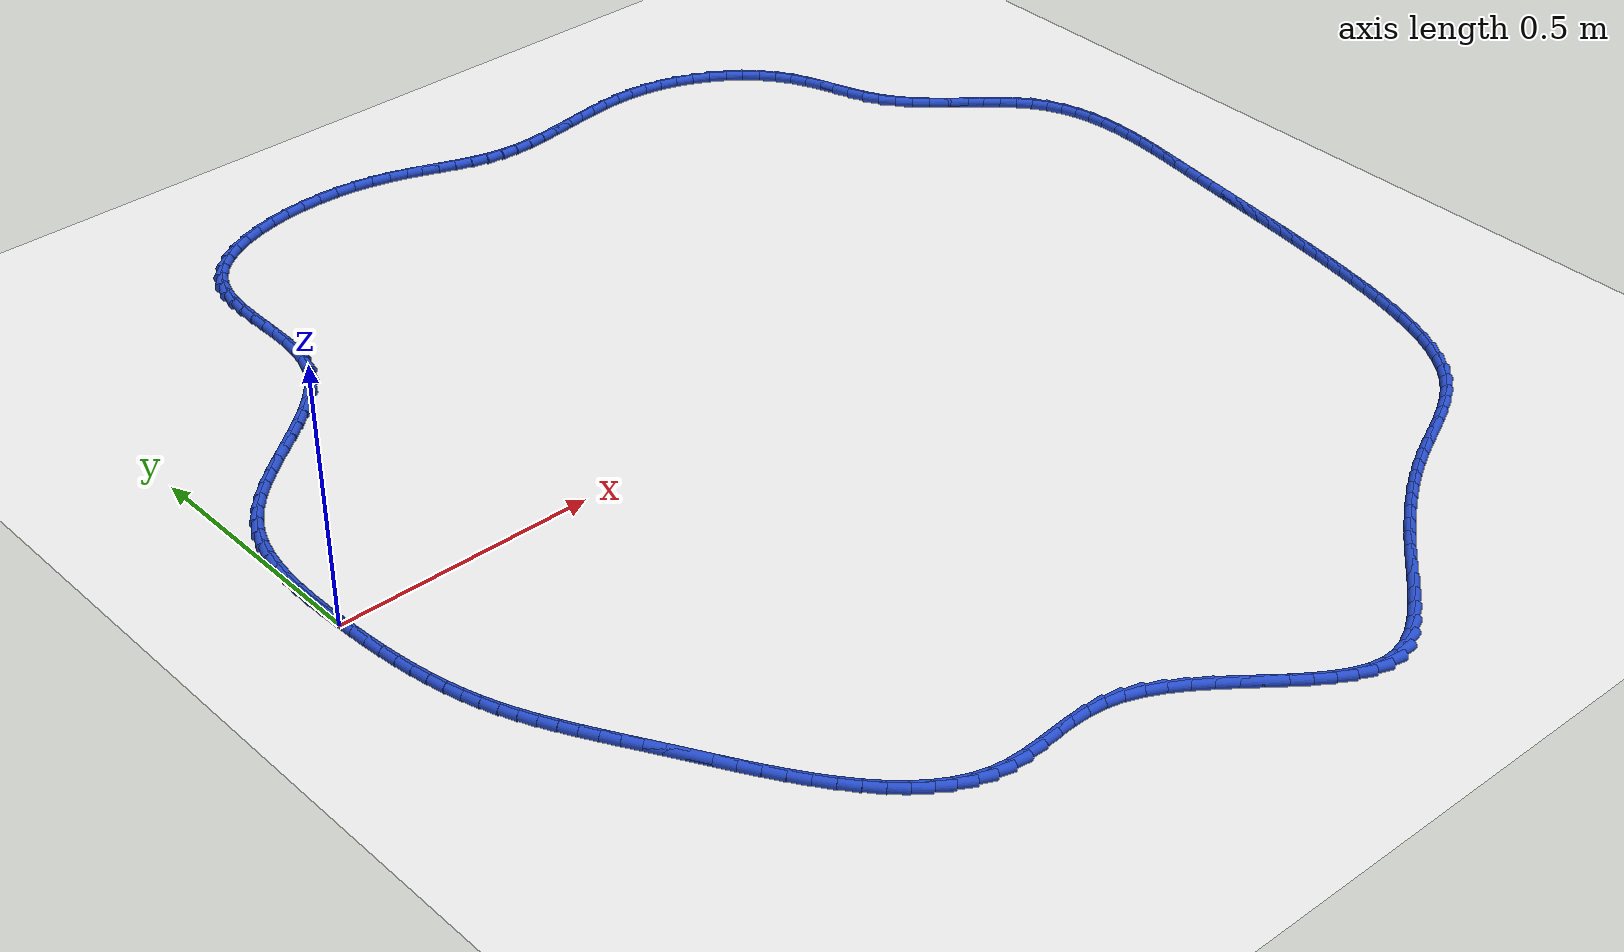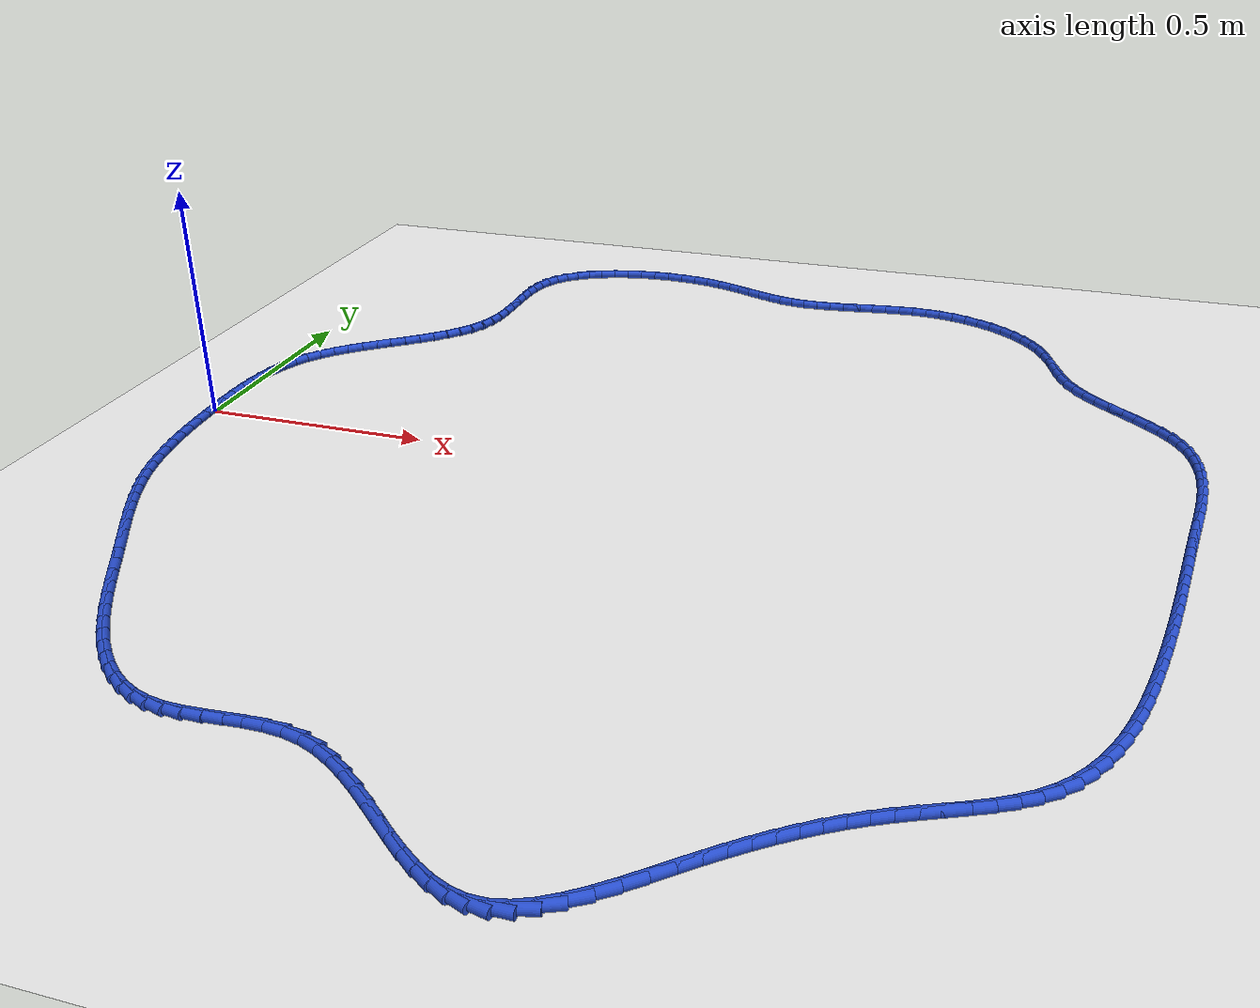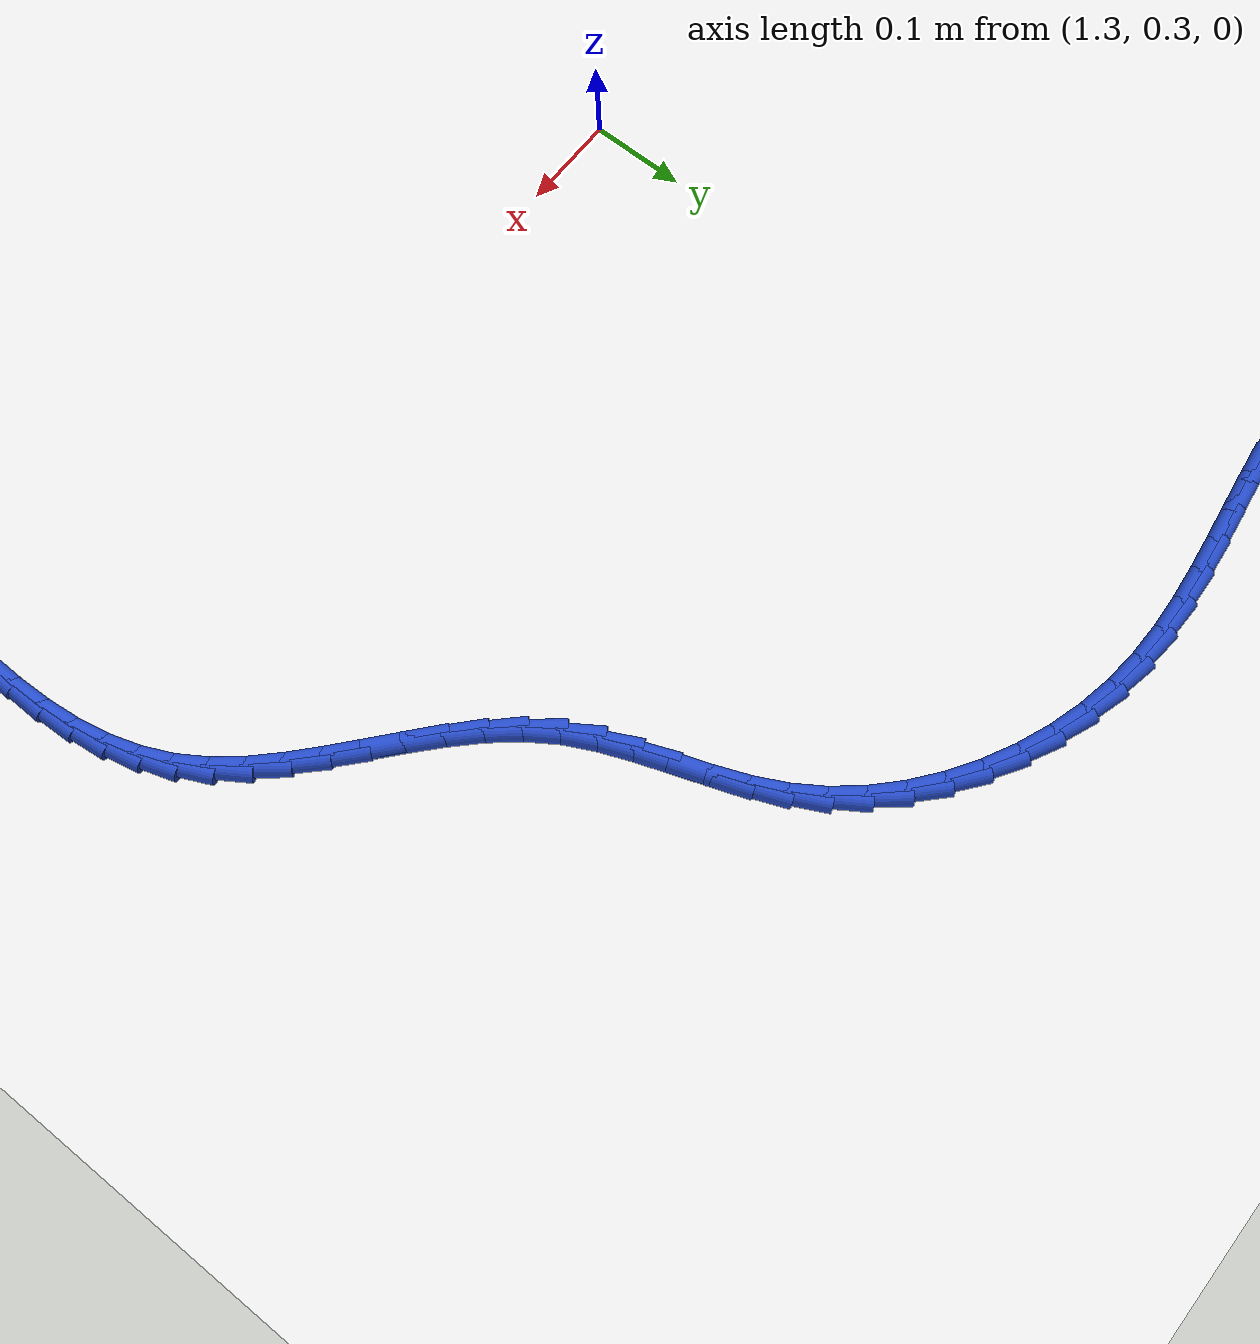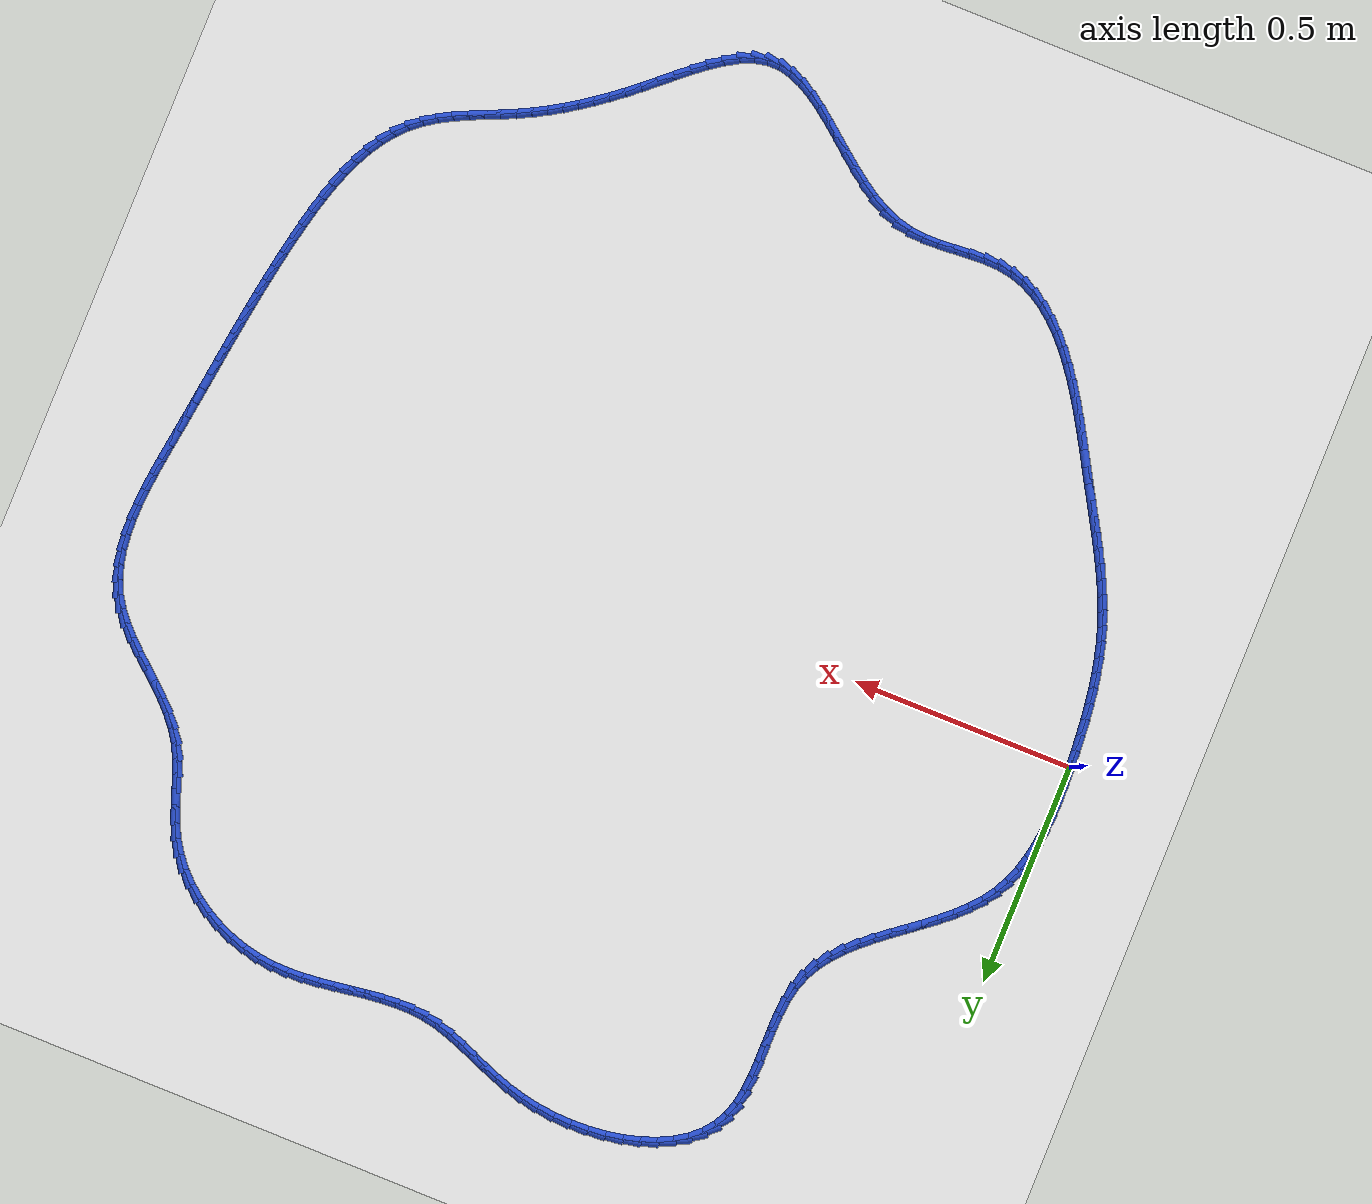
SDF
<sdf version="1.6">
 <world name="default">
  <light name="sun" type="directional">
   <pose>0 0 10 0 -0 0</pose>
   <diffuse>0.8 0.8 0.8 1</diffuse>
   <specular>0.2 0.2 0.2 1</specular>
   <attenuation>
    <range>1000</range>
    <constant>0.9</constant>
    <linear>0.01</linear>
    <quadratic>0.001</quadratic>
   </attenuation>
   <direction>-0.5 0.1 -0.9</direction>
  </light>
  <model name="ground_plane">
   <static>1</static>
   <link name="link">
    <collision name="collision">
     <geometry><plane><normal>0 0 1</normal><size>100 100</size></plane></geometry>
     <surface><friction><ode><mu>100</mu><mu2>50</mu2></ode></friction></surface>
    </collision>
    <visual name="visual">
     <cast_shadows>0</cast_shadows>
     <geometry><plane><normal>0 0 1</normal><size>100 100</size></plane></geometry>
     <material>
      <script><uri>file://media/materials/scripts/gazebo.material</uri><name>Gazebo/WhiteGlow</name></script>
     </material>
    </visual>
   </link>
  </model>
  <gravity>0 0 -9.8</gravity>
  <magnetic_field>6e-06 2.3e-05 -4.2e-05</magnetic_field>
  <atmosphere type="adiabatic"/>
  <physics name="default_physics" default="0" type="ode">
   <max_step_size>0.001</max_step_size>
   <real_time_factor>1</real_time_factor>
   <real_time_update_rate>1000</real_time_update_rate>
  </physics>
  <scene><ambient>0.4 0.4 0.4 1</ambient><background>0.7 0.7 0.7 1</background><shadows>1</shadows></scene>
  <spherical_coordinates>
   <surface_model>EARTH_WGS84</surface_model>
   <latitude_deg>0</latitude_deg>
   <longitude_deg>0</longitude_deg>
   <elevation>0</elevation>
   <heading_deg>0</heading_deg>
  </spherical_coordinates>
  <model name="line">
   <link name="link_0">
    <pose>9.269928574751063e-18 -8.326672684688674e-17 0.01 0 1.57 -1.5322040979564748</pose>
    <collision name="collision">
     <geometry><cylinder><radius>0.01</radius><length>0.08</length></cylinder></geometry>
    </collision>
    <visual name="visual">
     <material>
      <script><name>Gazebo/Blue</name><uri>file://media/materials/scripts/gazebo.material</uri></script>
     </material>
     <geometry><cylinder><radius>0.01</radius><length>0.08</length></cylinder></geometry>
    </visual>
   </link>
   <link name="link_1">
    <pose>-0.0014031627960501823 0.03634063551600718 0.01 0 1.57 -1.5551111960871016</pose>
    <collision name="collision">
     <geometry><cylinder><radius>0.01</radius><length>0.08</length></cylinder></geometry>
    </collision>
    <visual name="visual">
     <material>
      <script><name>Gazebo/Blue</name><uri>file://media/materials/scripts/gazebo.material</uri></script>
     </material>
     <geometry><cylinder><radius>0.01</radius><length>0.08</length></cylinder></geometry>
    </visual>
   </link>
   <link name="link_2">
    <pose>-0.0019743174826526277 0.07275141572233851 0.01 0 1.57 1.5534298415493895</pose>
    <collision name="collision">
     <geometry><cylinder><radius>0.01</radius><length>0.08</length></cylinder></geometry>
    </collision>
    <visual name="visual">
     <material>
      <script><name>Gazebo/Blue</name><uri>file://media/materials/scripts/gazebo.material</uri></script>
     </material>
     <geometry><cylinder><radius>0.01</radius><length>0.08</length></cylinder></geometry>
    </visual>
   </link>
   <link name="link_3">
    <pose>-0.0013451948375491857 0.10897402428306209 0.01 0 1.57 1.5094450359591003</pose>
    <collision name="collision">
     <geometry><cylinder><radius>0.01</radius><length>0.08</length></cylinder></geometry>
    </collision>
    <visual name="visual">
     <material>
      <script><name>Gazebo/Blue</name><uri>file://media/materials/scripts/gazebo.material</uri></script>
     </material>
     <geometry><cylinder><radius>0.01</radius><length>0.08</length></cylinder></geometry>
    </visual>
   </link>
   <link name="link_4">
    <pose>0.0008524743615182799 0.1447501448622461 0.01 0 1.57 1.4534500032611186</pose>
    <collision name="collision">
     <geometry><cylinder><radius>0.01</radius><length>0.08</length></cylinder></geometry>
    </collision>
    <visual name="visual">
     <material>
      <script><name>Gazebo/Blue</name><uri>file://media/materials/scripts/gazebo.material</uri></script>
     </material>
     <geometry><cylinder><radius>0.01</radius><length>0.08</length></cylinder></geometry>
    </visual>
   </link>
   <link name="link_5">
    <pose>0.0049869593368079106 0.17982146112395883 0.01 0 1.57 1.3841944477927413</pose>
    <collision name="collision">
     <geometry><cylinder><radius>0.01</radius><length>0.08</length></cylinder></geometry>
    </collision>
    <visual name="visual">
     <material>
      <script><name>Gazebo/Blue</name><uri>file://media/materials/scripts/gazebo.material</uri></script>
     </material>
     <geometry><cylinder><radius>0.01</radius><length>0.08</length></cylinder></geometry>
    </visual>
   </link>
   <link name="link_6">
    <pose>0.011426529310577839 0.21392965673226863 0.01 0 1.57 1.3004787172514183</pose>
    <collision name="collision">
     <geometry><cylinder><radius>0.01</radius><length>0.08</length></cylinder></geometry>
    </collision>
    <visual name="visual">
     <material>
      <script><name>Gazebo/Blue</name><uri>file://media/materials/scripts/gazebo.material</uri></script>
     </material>
     <geometry><cylinder><radius>0.01</radius><length>0.08</length></cylinder></geometry>
    </visual>
   </link>
   <link name="link_7">
    <pose>0.020539453505086215 0.24681641535124357 0.01 0 1.57 1.2015458215213368</pose>
    <collision name="collision">
     <geometry><cylinder><radius>0.01</radius><length>0.08</length></cylinder></geometry>
    </collision>
    <visual name="visual">
     <material>
      <script><name>Gazebo/Blue</name><uri>file://media/materials/scripts/gazebo.material</uri></script>
     </material>
     <geometry><cylinder><radius>0.01</radius><length>0.08</length></cylinder></geometry>
    </visual>
   </link>
   <link name="link_8">
    <pose>0.032694001142591154 0.27822342064495204 0.01 0 1.57 1.0876598648968587</pose>
    <collision name="collision">
     <geometry><cylinder><radius>0.01</radius><length>0.08</length></cylinder></geometry>
    </collision>
    <visual name="visual">
     <material>
      <script><name>Gazebo/Blue</name><uri>file://media/materials/scripts/gazebo.material</uri></script>
     </material>
     <geometry><cylinder><radius>0.01</radius><length>0.08</length></cylinder></geometry>
    </visual>
   </link>
   <link name="link_9">
    <pose>0.04825844144535081 0.3078923562774621 0.01 0 1.57 0.9658223907676853</pose>
    <collision name="collision">
     <geometry><cylinder><radius>0.01</radius><length>0.08</length></cylinder></geometry>
    </collision>
    <visual name="visual">
     <material>
      <script><name>Gazebo/Blue</name><uri>file://media/materials/scripts/gazebo.material</uri></script>
     </material>
     <geometry><cylinder><radius>0.01</radius><length>0.08</length></cylinder></geometry>
    </visual>
   </link>
   <link name="link_10">
    <pose>0.06745292896451253 0.3356515662217909 0.01 0 1.57 0.8614106802384787</pose>
    <collision name="collision">
     <geometry><cylinder><radius>0.01</radius><length>0.08</length></cylinder></geometry>
    </collision>
    <visual name="visual">
     <material>
      <script><name>Gazebo/Blue</name><uri>file://media/materials/scripts/gazebo.material</uri></script>
     </material>
     <geometry><cylinder><radius>0.01</radius><length>0.08</length></cylinder></geometry>
    </visual>
   </link>
   <link name="link_11">
    <pose>0.08983111288050157 0.36171935961044616 0.01 0 1.57 0.7808889226528758</pose>
    <collision name="collision">
     <geometry><cylinder><radius>0.01</radius><length>0.08</length></cylinder></geometry>
    </collision>
    <visual name="visual">
     <material>
      <script><name>Gazebo/Blue</name><uri>file://media/materials/scripts/gazebo.material</uri></script>
     </material>
     <geometry><cylinder><radius>0.01</radius><length>0.08</length></cylinder></geometry>
    </visual>
   </link>
   <link name="link_12">
    <pose>0.1147592477045748 0.38642368819137507 0.01 0 1.57 0.7226157922241102</pose>
    <collision name="collision">
     <geometry><cylinder><radius>0.01</radius><length>0.08</length></cylinder></geometry>
    </collision>
    <visual name="visual">
     <material>
      <script><name>Gazebo/Blue</name><uri>file://media/materials/scripts/gazebo.material</uri></script>
     </material>
     <geometry><cylinder><radius>0.01</radius><length>0.08</length></cylinder></geometry>
    </visual>
   </link>
   <link name="link_13">
    <pose>0.14160357787230773 0.41009250960769783 0.01 0 1.57 0.6846308907383529</pose>
    <collision name="collision">
     <geometry><cylinder><radius>0.01</radius><length>0.08</length></cylinder></geometry>
    </collision>
    <visual name="visual">
     <material>
      <script><name>Gazebo/Blue</name><uri>file://media/materials/scripts/gazebo.material</uri></script>
     </material>
     <geometry><cylinder><radius>0.01</radius><length>0.08</length></cylinder></geometry>
    </visual>
   </link>
   <link name="link_14">
    <pose>0.16973034781927573 0.43305378150253476 0.01 0 1.57 0.6653758053141456</pose>
    <collision name="collision">
     <geometry><cylinder><radius>0.01</radius><length>0.08</length></cylinder></geometry>
    </collision>
    <visual name="visual">
     <material>
      <script><name>Gazebo/Blue</name><uri>file://media/materials/scripts/gazebo.material</uri></script>
     </material>
     <geometry><cylinder><radius>0.01</radius><length>0.08</length></cylinder></geometry>
    </visual>
   </link>
   <link name="link_15">
    <pose>0.1985058019810543 0.4556354615190062 0.01 0 1.57 0.6640125981625362</pose>
    <collision name="collision">
     <geometry><cylinder><radius>0.01</radius><length>0.08</length></cylinder></geometry>
    </collision>
    <visual name="visual">
     <material>
      <script><name>Gazebo/Blue</name><uri>file://media/materials/scripts/gazebo.material</uri></script>
     </material>
     <geometry><cylinder><radius>0.01</radius><length>0.08</length></cylinder></geometry>
    </visual>
   </link>
   <link name="link_16">
    <pose>0.22729618479321892 0.47816550730023255 0.01 0 1.57 0.6805388929093404</pose>
    <collision name="collision">
     <geometry><cylinder><radius>0.01</radius><length>0.08</length></cylinder></geometry>
    </collision>
    <visual name="visual">
     <material>
      <script><name>Gazebo/Blue</name><uri>file://media/materials/scripts/gazebo.material</uri></script>
     </material>
     <geometry><cylinder><radius>0.01</radius><length>0.08</length></cylinder></geometry>
    </visual>
   </link>
   <link name="link_17">
    <pose>0.2554677406913451 0.500971876489334 0.01 0 1.57 0.7158038160591095</pose>
    <collision name="collision">
     <geometry><cylinder><radius>0.01</radius><length>0.08</length></cylinder></geometry>
    </collision>
    <visual name="visual">
     <material>
      <script><name>Gazebo/Blue</name><uri>file://media/materials/scripts/gazebo.material</uri></script>
     </material>
     <geometry><cylinder><radius>0.01</radius><length>0.08</length></cylinder></geometry>
    </visual>
   </link>
   <link name="link_18">
    <pose>0.2823867141110083 0.5243825267294309 0.01 0 1.57 0.7714296721098537</pose>
    <collision name="collision">
     <geometry><cylinder><radius>0.01</radius><length>0.08</length></cylinder></geometry>
    </collision>
    <visual name="visual">
     <material>
      <script><name>Gazebo/Blue</name><uri>file://media/materials/scripts/gazebo.material</uri></script>
     </material>
     <geometry><cylinder><radius>0.01</radius><length>0.08</length></cylinder></geometry>
    </visual>
   </link>
   <link name="link_19">
    <pose>0.3074193494877838 0.5487254156636434 0.01 0 1.57 0.8495416437112011</pose>
    <collision name="collision">
     <geometry><cylinder><radius>0.01</radius><length>0.08</length></cylinder></geometry>
    </collision>
    <visual name="visual">
     <material>
      <script><name>Gazebo/Blue</name><uri>file://media/materials/scripts/gazebo.material</uri></script>
     </material>
     <geometry><cylinder><radius>0.01</radius><length>0.08</length></cylinder></geometry>
    </visual>
   </link>
   <link name="link_20">
    <pose>0.3299318912572474 0.5743285009350921 0.01 0 1.57 0.9520978609148936</pose>
    <collision name="collision">
     <geometry><cylinder><radius>0.01</radius><length>0.08</length></cylinder></geometry>
    </collision>
    <visual name="visual">
     <material>
      <script><name>Gazebo/Blue</name><uri>file://media/materials/scripts/gazebo.material</uri></script>
     </material>
     <geometry><cylinder><radius>0.01</radius><length>0.08</length></cylinder></geometry>
    </visual>
   </link>
   <link name="link_21">
    <pose>0.34929058385497425 0.601519740186897 0.01 0 1.57 1.079578243119373</pose>
    <collision name="collision">
     <geometry><cylinder><radius>0.01</radius><length>0.08</length></cylinder></geometry>
    </collision>
    <visual name="visual">
     <material>
      <script><name>Gazebo/Blue</name><uri>file://media/materials/scripts/gazebo.material</uri></script>
     </material>
     <geometry><cylinder><radius>0.01</radius><length>0.08</length></cylinder></geometry>
    </visual>
   </link>
   <link name="link_22">
    <pose>0.36486167171654 0.6306270910621787 0.01 0 1.57 1.2282904424377823</pose>
    <collision name="collision">
     <geometry><cylinder><radius>0.01</radius><length>0.08</length></cylinder></geometry>
    </collision>
    <visual name="visual">
     <material>
      <script><name>Gazebo/Blue</name><uri>file://media/materials/scripts/gazebo.material</uri></script>
     </material>
     <geometry><cylinder><radius>0.01</radius><length>0.08</length></cylinder></geometry>
    </visual>
   </link>
   <link name="link_23">
    <pose>0.3760356930462408 0.6619655978491316 0.01 0 1.57 1.367348351773009</pose>
    <collision name="collision">
     <geometry><cylinder><radius>0.01</radius><length>0.08</length></cylinder></geometry>
    </collision>
    <visual name="visual">
     <material>
      <script><name>Gazebo/Blue</name><uri>file://media/materials/scripts/gazebo.material</uri></script>
     </material>
     <geometry><cylinder><radius>0.01</radius><length>0.08</length></cylinder></geometry>
    </visual>
   </link>
   <link name="link_24">
    <pose>0.3829448521581526 0.6954560721492837 0.01 0 1.57 1.4675712158796776</pose>
    <collision name="collision">
     <geometry><cylinder><radius>0.01</radius><length>0.08</length></cylinder></geometry>
    </collision>
    <visual name="visual">
     <material>
      <script><name>Gazebo/Blue</name><uri>file://media/materials/scripts/gazebo.material</uri></script>
     </material>
     <geometry><cylinder><radius>0.01</radius><length>0.08</length></cylinder></geometry>
    </visual>
   </link>
   <link name="link_25">
    <pose>0.3865815981031795 0.7305620623977352 0.01 0 1.57 1.5319614249728721</pose>
    <collision name="collision">
     <geometry><cylinder><radius>0.01</radius><length>0.08</length></cylinder></geometry>
    </collision>
    <visual name="visual">
     <material>
      <script><name>Gazebo/Blue</name><uri>file://media/materials/scripts/gazebo.material</uri></script>
     </material>
     <geometry><cylinder><radius>0.01</radius><length>0.08</length></cylinder></geometry>
    </visual>
   </link>
   <link name="link_26">
    <pose>0.3879865530885565 0.7667215105840509 0.01 0 1.57 1.5649633428570273</pose>
    <collision name="collision">
     <geometry><cylinder><radius>0.01</radius><length>0.08</length></cylinder></geometry>
    </collision>
    <visual name="visual">
     <material>
      <script><name>Gazebo/Blue</name><uri>file://media/materials/scripts/gazebo.material</uri></script>
     </material>
     <geometry><cylinder><radius>0.01</radius><length>0.08</length></cylinder></geometry>
    </visual>
   </link>
   <link name="link_27">
    <pose>0.38820033932151843 0.8033723586977951 0.01 0 1.57 1.569067532474074</pose>
    <collision name="collision">
     <geometry><cylinder><radius>0.01</radius><length>0.08</length></cylinder></geometry>
    </collision>
    <visual name="visual">
     <material>
      <script><name>Gazebo/Blue</name><uri>file://media/materials/scripts/gazebo.material</uri></script>
     </material>
     <geometry><cylinder><radius>0.01</radius><length>0.08</length></cylinder></geometry>
    </visual>
   </link>
   <link name="link_28">
    <pose>0.3882635790093003 0.8399525487285324 0.01 0 1.57 1.5442828655423926</pose>
    <collision name="collision">
     <geometry><cylinder><radius>0.01</radius><length>0.08</length></cylinder></geometry>
    </collision>
    <visual name="visual">
     <material>
      <script><name>Gazebo/Blue</name><uri>file://media/materials/scripts/gazebo.material</uri></script>
     </material>
     <geometry><cylinder><radius>0.01</radius><length>0.08</length></cylinder></geometry>
    </visual>
   </link>
   <link name="link_29">
    <pose>0.38921689435913703 0.8759000226658278 0.01 0 1.57 1.4879993091222576</pose>
    <collision name="collision">
     <geometry><cylinder><radius>0.01</radius><length>0.08</length></cylinder></geometry>
    </collision>
    <visual name="visual">
     <material>
      <script><name>Gazebo/Blue</name><uri>file://media/materials/scripts/gazebo.material</uri></script>
     </material>
     <geometry><cylinder><radius>0.01</radius><length>0.08</length></cylinder></geometry>
    </visual>
   </link>
   <link name="link_30">
    <pose>0.3921009075782636 0.9106527224992458 0.01 0 1.57 1.3951680918966898</pose>
    <collision name="collision">
     <geometry><cylinder><radius>0.01</radius><length>0.08</length></cylinder></geometry>
    </collision>
    <visual name="visual">
     <material>
      <script><name>Gazebo/Blue</name><uri>file://media/materials/scripts/gazebo.material</uri></script>
     </material>
     <geometry><cylinder><radius>0.01</radius><length>0.08</length></cylinder></geometry>
    </visual>
   </link>
   <link name="link_31">
    <pose>0.39795624087391496 0.9436485902183511 0.01 0 1.57 1.259596605212832</pose>
    <collision name="collision">
     <geometry><cylinder><radius>0.01</radius><length>0.08</length></cylinder></geometry>
    </collision>
    <visual name="visual">
     <material>
      <script><name>Gazebo/Blue</name><uri>file://media/materials/scripts/gazebo.material</uri></script>
     </material>
     <geometry><cylinder><radius>0.01</radius><length>0.08</length></cylinder></geometry>
    </visual>
   </link>
   <link name="link_32">
    <pose>0.40782351645332593 0.9743255678127083 0.01 0 1.57 1.0803814110568757</pose>
    <collision name="collision">
     <geometry><cylinder><radius>0.01</radius><length>0.08</length></cylinder></geometry>
    </collision>
    <visual name="visual">
     <material>
      <script><name>Gazebo/Blue</name><uri>file://media/materials/scripts/gazebo.material</uri></script>
     </material>
     <geometry><cylinder><radius>0.01</radius><length>0.08</length></cylinder></geometry>
    </visual>
   </link>
   <link name="link_33">
    <pose>0.4226773873524218 1.0021459094666414 0.01 0 1.57 0.8931537006835075</pose>
    <collision name="collision">
     <geometry><cylinder><radius>0.01</radius><length>0.08</length></cylinder></geometry>
    </collision>
    <visual name="visual">
     <material>
      <script><name>Gazebo/Blue</name><uri>file://media/materials/scripts/gazebo.material</uri></script>
     </material>
     <geometry><cylinder><radius>0.01</radius><length>0.08</length></cylinder></geometry>
    </visual>
   </link>
   <link name="link_34">
    <pose>0.4425995147955887 1.026900971434573 0.01 0 1.57 0.7266991034931036</pose>
    <collision name="collision">
     <geometry><cylinder><radius>0.01</radius><length>0.08</length></cylinder></geometry>
    </collision>
    <visual name="visual">
     <material>
      <script><name>Gazebo/Blue</name><uri>file://media/materials/scripts/gazebo.material</uri></script>
     </material>
     <geometry><cylinder><radius>0.01</radius><length>0.08</length></cylinder></geometry>
    </visual>
   </link>
   <link name="link_35">
    <pose>0.4670292913351283 1.048618810853073 0.01 0 1.57 0.5832376141481203</pose>
    <collision name="collision">
     <geometry><cylinder><radius>0.01</radius><length>0.08</length></cylinder></geometry>
    </collision>
    <visual name="visual">
     <material>
      <script><name>Gazebo/Blue</name><uri>file://media/materials/scripts/gazebo.material</uri></script>
     </material>
     <geometry><cylinder><radius>0.01</radius><length>0.08</length></cylinder></geometry>
    </visual>
   </link>
   <link name="link_36">
    <pose>0.49539199859865535 1.067332685281007 0.01 0 1.57 0.4606851171406325</pose>
    <collision name="collision">
     <geometry><cylinder><radius>0.01</radius><length>0.08</length></cylinder></geometry>
    </collision>
    <visual name="visual">
     <material>
      <script><name>Gazebo/Blue</name><uri>file://media/materials/scripts/gazebo.material</uri></script>
     </material>
     <geometry><cylinder><radius>0.01</radius><length>0.08</length></cylinder></geometry>
    </visual>
   </link>
   <link name="link_37">
    <pose>0.5271129182137849 1.0830758522772401 0.01 0 1.57 0.3553758814538861</pose>
    <collision name="collision">
     <geometry><cylinder><radius>0.01</radius><length>0.08</length></cylinder></geometry>
    </collision>
    <visual name="visual">
     <material>
      <script><name>Gazebo/Blue</name><uri>file://media/materials/scripts/gazebo.material</uri></script>
     </material>
     <geometry><cylinder><radius>0.01</radius><length>0.08</length></cylinder></geometry>
    </visual>
   </link>
   <link name="link_38">
    <pose>0.5616173318081314 1.0958815694006372 0.01 0 1.57 0.2634316306784564</pose>
    <collision name="collision">
     <geometry><cylinder><radius>0.01</radius><length>0.08</length></cylinder></geometry>
    </collision>
    <visual name="visual">
     <material>
      <script><name>Gazebo/Blue</name><uri>file://media/materials/scripts/gazebo.material</uri></script>
     </material>
     <geometry><cylinder><radius>0.01</radius><length>0.08</length></cylinder></geometry>
    </visual>
   </link>
   <link name="link_39">
    <pose>0.59833052100931 1.105783094210063 0.01 0 1.57 0.1813263729452793</pose>
    <collision name="collision">
     <geometry><cylinder><radius>0.01</radius><length>0.08</length></cylinder></geometry>
    </collision>
    <visual name="visual">
     <material>
      <script><name>Gazebo/Blue</name><uri>file://media/materials/scripts/gazebo.material</uri></script>
     </material>
     <geometry><cylinder><radius>0.01</radius><length>0.08</length></cylinder></geometry>
    </visual>
   </link>
   <link name="link_40">
    <pose>0.636677767444935 1.1128136842643828 0.01 0 1.57 0.10600249813779578</pose>
    <collision name="collision">
     <geometry><cylinder><radius>0.01</radius><length>0.08</length></cylinder></geometry>
    </collision>
    <visual name="visual">
     <material>
      <script><name>Gazebo/Blue</name><uri>file://media/materials/scripts/gazebo.material</uri></script>
     </material>
     <geometry><cylinder><radius>0.01</radius><length>0.08</length></cylinder></geometry>
    </visual>
   </link>
   <link name="link_41">
    <pose>0.6760843527426215 1.1170065971224616 0.01 0 1.57 0.03479295418843869</pose>
    <collision name="collision">
     <geometry><cylinder><radius>0.01</radius><length>0.08</length></cylinder></geometry>
    </collision>
    <visual name="visual">
     <material>
      <script><name>Gazebo/Blue</name><uri>file://media/materials/scripts/gazebo.material</uri></script>
     </material>
     <geometry><cylinder><radius>0.01</radius><length>0.08</length></cylinder></geometry>
    </visual>
   </link>
   <link name="link_42">
    <pose>0.7159755585299838 1.1183950903431639 0.01 0 1.57 -0.03472549176726358</pose>
    <collision name="collision">
     <geometry><cylinder><radius>0.01</radius><length>0.08</length></cylinder></geometry>
    </collision>
    <visual name="visual">
     <material>
      <script><name>Gazebo/Blue</name><uri>file://media/materials/scripts/gazebo.material</uri></script>
     </material>
     <geometry><cylinder><radius>0.01</radius><length>0.08</length></cylinder></geometry>
    </visual>
   </link>
   <link name="link_43">
    <pose>0.7557766664346373 1.117012421485355 0.01 0 1.57 -0.10490129377826278</pose>
    <collision name="collision">
     <geometry><cylinder><radius>0.01</radius><length>0.08</length></cylinder></geometry>
    </collision>
    <visual name="visual">
     <material>
      <script><name>Gazebo/Blue</name><uri>file://media/materials/scripts/gazebo.material</uri></script>
     </material>
     <geometry><cylinder><radius>0.01</radius><length>0.08</length></cylinder></geometry>
    </visual>
   </link>
   <link name="link_44">
    <pose>0.7949129580841965 1.1128918481079002 0.01 0 1.57 -0.17819016622875455</pose>
    <collision name="collision">
     <geometry><cylinder><radius>0.01</radius><length>0.08</length></cylinder></geometry>
    </collision>
    <visual name="visual">
     <material>
      <script><name>Gazebo/Blue</name><uri>file://media/materials/scripts/gazebo.material</uri></script>
     </material>
     <geometry><cylinder><radius>0.01</radius><length>0.08</length></cylinder></geometry>
    </visual>
   </link>
   <link name="link_45">
    <pose>0.8328097151062761 1.1060666277696636 0.01 0 1.57 -0.254091544635744</pose>
    <collision name="collision">
     <geometry><cylinder><radius>0.01</radius><length>0.08</length></cylinder></geometry>
    </collision>
    <visual name="visual">
     <material>
      <script><name>Gazebo/Blue</name><uri>file://media/materials/scripts/gazebo.material</uri></script>
     </material>
     <geometry><cylinder><radius>0.01</radius><length>0.08</length></cylinder></geometry>
    </visual>
   </link>
   <link name="link_46">
    <pose>0.86900593768435 1.0966662944829169 0.01 0 1.57 -0.3166018478970904</pose>
    <collision name="collision">
     <geometry><cylinder><radius>0.01</radius><length>0.08</length></cylinder></geometry>
    </collision>
    <visual name="visual">
     <material>
      <script><name>Gazebo/Blue</name><uri>file://media/materials/scripts/gazebo.material</uri></script>
     </material>
     <geometry><cylinder><radius>0.01</radius><length>0.08</length></cylinder></geometry>
    </visual>
   </link>
   <link name="link_47">
    <pose>0.9036328284124631 1.0853217529232981 0.01 0 1.57 -0.3581747486524444</pose>
    <collision name="collision">
     <geometry><cylinder><radius>0.01</radius><length>0.08</length></cylinder></geometry>
    </collision>
    <visual name="visual">
     <material>
      <script><name>Gazebo/Blue</name><uri>file://media/materials/scripts/gazebo.material</uri></script>
     </material>
     <geometry><cylinder><radius>0.01</radius><length>0.08</length></cylinder></geometry>
    </visual>
   </link>
   <link name="link_48">
    <pose>0.9370137480322254 1.072826592781226 0.01 0 1.57 -0.377015366398424</pose>
    <collision name="collision">
     <geometry><cylinder><radius>0.01</radius><length>0.08</length></cylinder></geometry>
    </collision>
    <visual name="visual">
     <material>
      <script><name>Gazebo/Blue</name><uri>file://media/materials/scripts/gazebo.material</uri></script>
     </material>
     <geometry><cylinder><radius>0.01</radius><length>0.08</length></cylinder></geometry>
    </visual>
   </link>
   <link name="link_49">
    <pose>0.9694721577611478 1.0599744888120681 0.01 0 1.57 -0.37158965942968897</pose>
    <collision name="collision">
     <geometry><cylinder><radius>0.01</radius><length>0.08</length></cylinder></geometry>
    </collision>
    <visual name="visual">
     <material>
      <script><name>Gazebo/Blue</name><uri>file://media/materials/scripts/gazebo.material</uri></script>
     </material>
     <geometry><cylinder><radius>0.01</radius><length>0.08</length></cylinder></geometry>
    </visual>
   </link>
   <link name="link_50">
    <pose>1.001331518816741 1.0475591157711936 0.01 0 1.57 -0.3403551428548425</pose>
    <collision name="collision">
     <geometry><cylinder><radius>0.01</radius><length>0.08</length></cylinder></geometry>
    </collision>
    <visual name="visual">
     <material>
      <script><name>Gazebo/Blue</name><uri>file://media/materials/scripts/gazebo.material</uri></script>
     </material>
     <geometry><cylinder><radius>0.01</radius><length>0.08</length></cylinder></geometry>
    </visual>
   </link>
   <link name="link_51">
    <pose>1.0329152924165161 1.036374148413972 0.01 0 1.57 -0.2818989669265441</pose>
    <collision name="collision">
     <geometry><cylinder><radius>0.01</radius><length>0.08</length></cylinder></geometry>
    </collision>
    <visual name="visual">
     <material>
      <script><name>Gazebo/Blue</name><uri>file://media/materials/scripts/gazebo.material</uri></script>
     </material>
     <geometry><cylinder><radius>0.01</radius><length>0.08</length></cylinder></geometry>
    </visual>
   </link>
   <link name="link_52">
    <pose>1.0645469397779832 1.0272132614957707 0.01 0 1.57 -0.19566842280877916</pose>
    <collision name="collision">
     <geometry><cylinder><radius>0.01</radius><length>0.08</length></cylinder></geometry>
    </collision>
    <visual name="visual">
     <material>
      <script><name>Gazebo/Blue</name><uri>file://media/materials/scripts/gazebo.material</uri></script>
     </material>
     <geometry><cylinder><radius>0.01</radius><length>0.08</length></cylinder></geometry>
    </visual>
   </link>
   <link name="link_53">
    <pose>1.0965499221033381 1.0208701297156095 0.01 0 1.57 -0.0910905827970096</pose>
    <collision name="collision">
     <geometry><cylinder><radius>0.01</radius><length>0.08</length></cylinder></geometry>
    </collision>
    <visual name="visual">
     <material>
      <script><name>Gazebo/Blue</name><uri>file://media/materials/scripts/gazebo.material</uri></script>
     </material>
     <geometry><cylinder><radius>0.01</radius><length>0.08</length></cylinder></geometry>
    </visual>
   </link>
   <link name="link_54">
    <pose>1.1291800683508 1.0178895824220704 0.01 0 1.57 -0.001515008681421192</pose>
    <collision name="collision">
     <geometry><cylinder><radius>0.01</radius><length>0.08</length></cylinder></geometry>
    </collision>
    <visual name="visual">
     <material>
      <script><name>Gazebo/Blue</name><uri>file://media/materials/scripts/gazebo.material</uri></script>
     </material>
     <geometry><cylinder><radius>0.01</radius><length>0.08</length></cylinder></geometry>
    </visual>
   </link>
   <link name="link_55">
    <pose>1.1624276098938178 1.0178392120694593 0.01 0 1.57 0.06523859716427143</pose>
    <collision name="collision">
     <geometry><cylinder><radius>0.01</radius><length>0.08</length></cylinder></geometry>
    </collision>
    <visual name="visual">
     <material>
      <script><name>Gazebo/Blue</name><uri>file://media/materials/scripts/gazebo.material</uri></script>
     </material>
     <geometry><cylinder><radius>0.01</radius><length>0.08</length></cylinder></geometry>
    </visual>
   </link>
   <link name="link_56">
    <pose>1.196217589165755 1.0200467556276749 0.01 0 1.57 0.11027687657508883</pose>
    <collision name="collision">
     <geometry><cylinder><radius>0.01</radius><length>0.08</length></cylinder></geometry>
    </collision>
    <visual name="visual">
     <material>
      <script><name>Gazebo/Blue</name><uri>file://media/materials/scripts/gazebo.material</uri></script>
     </material>
     <geometry><cylinder><radius>0.01</radius><length>0.08</length></cylinder></geometry>
    </visual>
   </link>
   <link name="link_57">
    <pose>1.230475048599974 1.0238399500666189 0.01 0 1.57 0.13500591390225855</pose>
    <collision name="collision">
     <geometry><cylinder><radius>0.01</radius><length>0.08</length></cylinder></geometry>
    </collision>
    <visual name="visual">
     <material>
      <script><name>Gazebo/Blue</name><uri>file://media/materials/scripts/gazebo.material</uri></script>
     </material>
     <geometry><cylinder><radius>0.01</radius><length>0.08</length></cylinder></geometry>
    </visual>
   </link>
   <link name="link_58">
    <pose>1.2651250306298376 1.02854653235619 0.01 0 1.57 0.14056117292467457</pose>
    <collision name="collision">
     <geometry><cylinder><radius>0.01</radius><length>0.08</length></cylinder></geometry>
    </collision>
    <visual name="visual">
     <material>
      <script><name>Gazebo/Blue</name><uri>file://media/materials/scripts/gazebo.material</uri></script>
     </material>
     <geometry><cylinder><radius>0.01</radius><length>0.08</length></cylinder></geometry>
    </visual>
   </link>
   <link name="link_59">
    <pose>1.3000925776887093 1.0334942394662894 0.01 0 1.57 0.1275779175493634</pose>
    <collision name="collision">
     <geometry><cylinder><radius>0.01</radius><length>0.08</length></cylinder></geometry>
    </collision>
    <visual name="visual">
     <material>
      <script><name>Gazebo/Blue</name><uri>file://media/materials/scripts/gazebo.material</uri></script>
     </material>
     <geometry><cylinder><radius>0.01</radius><length>0.08</length></cylinder></geometry>
    </visual>
   </link>
   <link name="link_60">
    <pose>1.3353027322099518 1.0380108083668165 0.01 0 1.57 0.09617998112501255</pose>
    <collision name="collision">
     <geometry><cylinder><radius>0.01</radius><length>0.08</length></cylinder></geometry>
    </collision>
    <visual name="visual">
     <material>
      <script><name>Gazebo/Blue</name><uri>file://media/materials/scripts/gazebo.material</uri></script>
     </material>
     <geometry><cylinder><radius>0.01</radius><length>0.08</length></cylinder></geometry>
    </visual>
   </link>
   <link name="link_61">
    <pose>1.3706805366269272 1.0414239760276713 0.01 0 1.57 0.04613246864003099</pose>
    <collision name="collision">
     <geometry><cylinder><radius>0.01</radius><length>0.08</length></cylinder></geometry>
    </collision>
    <visual name="visual">
     <material>
      <script><name>Gazebo/Blue</name><uri>file://media/materials/scripts/gazebo.material</uri></script>
     </material>
     <geometry><cylinder><radius>0.01</radius><length>0.08</length></cylinder></geometry>
    </visual>
   </link>
   <link name="link_62">
    <pose>1.4061510333729998 1.043061479418755 0.01 0 1.57 -0.022832444425832977</pose>
    <collision name="collision">
     <geometry><cylinder><radius>0.01</radius><length>0.08</length></cylinder></geometry>
    </collision>
    <visual name="visual">
     <material>
      <script><name>Gazebo/Blue</name><uri>file://media/materials/scripts/gazebo.material</uri></script>
     </material>
     <geometry><cylinder><radius>0.01</radius><length>0.08</length></cylinder></geometry>
    </visual>
   </link>
   <link name="link_63">
    <pose>1.4416392648815313 1.0422510555099664 0.01 0 1.57 -0.1103382181605313</pose>
    <collision name="collision">
     <geometry><cylinder><radius>0.01</radius><length>0.08</length></cylinder></geometry>
    </collision>
    <visual name="visual">
     <material>
      <script><name>Gazebo/Blue</name><uri>file://media/materials/scripts/gazebo.material</uri></script>
     </material>
     <geometry><cylinder><radius>0.01</radius><length>0.08</length></cylinder></geometry>
    </visual>
   </link>
   <link name="link_64">
    <pose>1.4770681905299143 1.038325949274656 0.01 0 1.57 -0.20709685738291175</pose>
    <collision name="collision">
     <geometry><cylinder><radius>0.01</radius><length>0.08</length></cylinder></geometry>
    </collision>
    <visual name="visual">
     <material>
      <script><name>Gazebo/Blue</name><uri>file://media/materials/scripts/gazebo.material</uri></script>
     </material>
     <geometry><cylinder><radius>0.01</radius><length>0.08</length></cylinder></geometry>
    </visual>
   </link>
   <link name="link_65">
    <pose>1.5122411168408423 1.0309357910093828 0.01 0 1.57 -0.30103909492169634</pose>
    <collision name="collision">
     <geometry><cylinder><radius>0.01</radius><length>0.08</length></cylinder></geometry>
    </collision>
    <visual name="visual">
     <material>
      <script><name>Gazebo/Blue</name><uri>file://media/materials/scripts/gazebo.material</uri></script>
     </material>
     <geometry><cylinder><radius>0.01</radius><length>0.08</length></cylinder></geometry>
    </visual>
   </link>
   <link name="link_66">
    <pose>1.5467788901971713 1.020212670960871 0.01 0 1.57 -0.39279809596097404</pose>
    <collision name="collision">
     <geometry><cylinder><radius>0.01</radius><length>0.08</length></cylinder></geometry>
    </collision>
    <visual name="visual">
     <material>
      <script><name>Gazebo/Blue</name><uri>file://media/materials/scripts/gazebo.material</uri></script>
     </material>
     <geometry><cylinder><radius>0.01</radius><length>0.08</length></cylinder></geometry>
    </visual>
   </link>
   <link name="link_67">
    <pose>1.5802870071575774 1.0063292672840607 0.01 0 1.57 -0.4841048140478903</pose>
    <collision name="collision">
     <geometry><cylinder><radius>0.01</radius><length>0.08</length></cylinder></geometry>
    </collision>
    <visual name="visual">
     <material>
      <script><name>Gazebo/Blue</name><uri>file://media/materials/scripts/gazebo.material</uri></script>
     </material>
     <geometry><cylinder><radius>0.01</radius><length>0.08</length></cylinder></geometry>
    </visual>
   </link>
   <link name="link_68">
    <pose>1.6123709642807358 0.9894582581338924 0.01 0 1.57 -0.5766886230052523</pose>
    <collision name="collision">
     <geometry><cylinder><radius>0.01</radius><length>0.08</length></cylinder></geometry>
    </collision>
    <visual name="visual">
     <material>
      <script><name>Gazebo/Blue</name><uri>file://media/materials/scripts/gazebo.material</uri></script>
     </material>
     <geometry><cylinder><radius>0.01</radius><length>0.08</length></cylinder></geometry>
    </visual>
   </link>
   <link name="link_69">
    <pose>1.6426362581253238 0.9697723216653069 0.01 0 1.57 -0.6722686207958498</pose>
    <collision name="collision">
     <geometry><cylinder><radius>0.01</radius><length>0.08</length></cylinder></geometry>
    </collision>
    <visual name="visual">
     <material>
      <script><name>Gazebo/Blue</name><uri>file://media/materials/scripts/gazebo.material</uri></script>
     </material>
     <geometry><cylinder><radius>0.01</radius><length>0.08</length></cylinder></geometry>
    </visual>
   </link>
   <link name="link_70">
    <pose>1.670688385250016 0.9474441360332443 0.01 0 1.57 -0.7725272215130539</pose>
    <collision name="collision">
     <geometry><cylinder><radius>0.01</radius><length>0.08</length></cylinder></geometry>
    </collision>
    <visual name="visual">
     <material>
      <script><name>Gazebo/Blue</name><uri>file://media/materials/scripts/gazebo.material</uri></script>
     </material>
     <geometry><cylinder><radius>0.01</radius><length>0.08</length></cylinder></geometry>
    </visual>
   </link>
   <link name="link_71">
    <pose>1.6961328422134891 0.9226463793926456 0.01 0 1.57 -0.8790406072689028</pose>
    <collision name="collision">
     <geometry><cylinder><radius>0.01</radius><length>0.08</length></cylinder></geometry>
    </collision>
    <visual name="visual">
     <material>
      <script><name>Gazebo/Blue</name><uri>file://media/materials/scripts/gazebo.material</uri></script>
     </material>
     <geometry><cylinder><radius>0.01</radius><length>0.08</length></cylinder></geometry>
    </visual>
   </link>
   <link name="link_72">
    <pose>1.7185751255744197 0.8955517298984504 0.01 0 1.57 -0.9931387269546321</pose>
    <collision name="collision">
     <geometry><cylinder><radius>0.01</radius><length>0.08</length></cylinder></geometry>
    </collision>
    <visual name="visual">
     <material>
      <script><name>Gazebo/Blue</name><uri>file://media/materials/scripts/gazebo.material</uri></script>
     </material>
     <geometry><cylinder><radius>0.01</radius><length>0.08</length></cylinder></geometry>
    </visual>
   </link>
   <link name="link_73">
    <pose>1.7376207323085797 0.8663328658355247 0.01 0 1.57 -1.1072463781847635</pose>
    <collision name="collision">
     <geometry><cylinder><radius>0.01</radius><length>0.08</length></cylinder></geometry>
    </collision>
    <visual name="visual">
     <material>
      <script><name>Gazebo/Blue</name><uri>file://media/materials/scripts/gazebo.material</uri></script>
     </material>
     <geometry><cylinder><radius>0.01</radius><length>0.08</length></cylinder></geometry>
    </visual>
   </link>
   <link name="link_74">
    <pose>1.753158074486359 0.8352505930832348 0.01 0 1.57 -1.188345618046412</pose>
    <collision name="collision">
     <geometry><cylinder><radius>0.01</radius><length>0.08</length></cylinder></geometry>
    </collision>
    <visual name="visual">
     <material>
      <script><name>Gazebo/Blue</name><uri>file://media/materials/scripts/gazebo.material</uri></script>
     </material>
     <geometry><cylinder><radius>0.01</radius><length>0.08</length></cylinder></geometry>
    </visual>
   </link>
   <link name="link_75">
    <pose>1.7661688136119358 0.8029062629517916 0.01 0 1.57 -1.2285351684633101</pose>
    <collision name="collision">
     <geometry><cylinder><radius>0.01</radius><length>0.08</length></cylinder></geometry>
    </collision>
    <visual name="visual">
     <material>
      <script><name>Gazebo/Blue</name><uri>file://media/materials/scripts/gazebo.material</uri></script>
     </material>
     <geometry><cylinder><radius>0.01</radius><length>0.08</length></cylinder></geometry>
    </visual>
   </link>
   <link name="link_76">
    <pose>1.7778986445909506 0.7699834727290222 0.01 0 1.57 -1.228474457304217</pose>
    <collision name="collision">
     <geometry><cylinder><radius>0.01</radius><length>0.08</length></cylinder></geometry>
    </collision>
    <visual name="visual">
     <material>
      <script><name>Gazebo/Blue</name><uri>file://media/materials/scripts/gazebo.material</uri></script>
     </material>
     <geometry><cylinder><radius>0.01</radius><length>0.08</length></cylinder></geometry>
    </visual>
   </link>
   <link name="link_77">
    <pose>1.789593262329044 0.7371658197027526 0.01 0 1.57 -1.1877750430193321</pose>
    <collision name="collision">
     <geometry><cylinder><radius>0.01</radius><length>0.08</length></cylinder></geometry>
    </collision>
    <visual name="visual">
     <material>
      <script><name>Gazebo/Blue</name><uri>file://media/materials/scripts/gazebo.material</uri></script>
     </material>
     <geometry><cylinder><radius>0.01</radius><length>0.08</length></cylinder></geometry>
    </visual>
   </link>
   <link name="link_78">
    <pose>1.8024983617318575 0.7051369011608095 0.01 0 1.57 -1.1049785169353048</pose>
    <collision name="collision">
     <geometry><cylinder><radius>0.01</radius><length>0.08</length></cylinder></geometry>
    </collision>
    <visual name="visual">
     <material>
      <script><name>Gazebo/Blue</name><uri>file://media/materials/scripts/gazebo.material</uri></script>
     </material>
     <geometry><cylinder><radius>0.01</radius><length>0.08</length></cylinder></geometry>
    </visual>
   </link>
   <link name="link_79">
    <pose>1.8178596377050327 0.6745803143910197 0.01 0 1.57 -0.9848775909268559</pose>
    <collision name="collision">
     <geometry><cylinder><radius>0.01</radius><length>0.08</length></cylinder></geometry>
    </collision>
    <visual name="visual">
     <material>
      <script><name>Gazebo/Blue</name><uri>file://media/materials/scripts/gazebo.material</uri></script>
     </material>
     <geometry><cylinder><radius>0.01</radius><length>0.08</length></cylinder></geometry>
    </visual>
   </link>
   <link name="link_80">
    <pose>1.8367650013761105 0.6460938293238604 0.01 0 1.57 -0.8732828910092946</pose>
    <collision name="collision">
     <geometry><cylinder><radius>0.01</radius><length>0.08</length></cylinder></geometry>
    </collision>
    <visual name="visual">
     <material>
      <script><name>Gazebo/Blue</name><uri>file://media/materials/scripts/gazebo.material</uri></script>
     </material>
     <geometry><cylinder><radius>0.01</radius><length>0.08</length></cylinder></geometry>
    </visual>
   </link>
   <link name="link_81">
    <pose>1.8589971825962617 0.6195652553275683 0.01 0 1.57 -0.7921494863658731</pose>
    <collision name="collision">
     <geometry><cylinder><radius>0.01</radius><length>0.08</length></cylinder></geometry>
    </collision>
    <visual name="visual">
     <material>
      <script><name>Gazebo/Blue</name><uri>file://media/materials/scripts/gazebo.material</uri></script>
     </material>
     <geometry><cylinder><radius>0.01</radius><length>0.08</length></cylinder></geometry>
    </visual>
   </link>
   <link name="link_82">
    <pose>1.8836947030084998 0.5945319811583597 0.01 0 1.57 -0.7398277532076821</pose>
    <collision name="collision">
     <geometry><cylinder><radius>0.01</radius><length>0.08</length></cylinder></geometry>
    </collision>
    <visual name="visual">
     <material>
      <script><name>Gazebo/Blue</name><uri>file://media/materials/scripts/gazebo.material</uri></script>
     </material>
     <geometry><cylinder><radius>0.01</radius><length>0.08</length></cylinder></geometry>
    </visual>
   </link>
   <link name="link_83">
    <pose>1.9099915369198925 0.5705289220239534 0.01 0 1.57 -0.7143404378488177</pose>
    <collision name="collision">
     <geometry><cylinder><radius>0.01</radius><length>0.08</length></cylinder></geometry>
    </collision>
    <visual name="visual">
     <material>
      <script><name>Gazebo/Blue</name><uri>file://media/materials/scripts/gazebo.material</uri></script>
     </material>
     <geometry><cylinder><radius>0.01</radius><length>0.08</length></cylinder></geometry>
    </visual>
   </link>
   <link name="link_84">
    <pose>1.9370216586375075 0.5470909931320691 0.01 0 1.57 -0.7146597867275178</pose>
    <collision name="collision">
     <geometry><cylinder><radius>0.01</radius><length>0.08</length></cylinder></geometry>
    </collision>
    <visual name="visual">
     <material>
      <script><name>Gazebo/Blue</name><uri>file://media/materials/scripts/gazebo.material</uri></script>
     </material>
     <geometry><cylinder><radius>0.01</radius><length>0.08</length></cylinder></geometry>
    </visual>
   </link>
   <link name="link_85">
    <pose>1.963919042468414 0.5237531096904255 0.01 0 1.57 -0.7411603266313025</pose>
    <collision name="collision">
     <geometry><cylinder><radius>0.01</radius><length>0.08</length></cylinder></geometry>
    </collision>
    <visual name="visual">
     <material>
      <script><name>Gazebo/Blue</name><uri>file://media/materials/scripts/gazebo.material</uri></script>
     </material>
     <geometry><cylinder><radius>0.01</radius><length>0.08</length></cylinder></geometry>
    </visual>
   </link>
   <link name="link_86">
    <pose>1.989817662719679 0.5000501869067417 0.01 0 1.57 -0.7956767396665315</pose>
    <collision name="collision">
     <geometry><cylinder><radius>0.01</radius><length>0.08</length></cylinder></geometry>
    </collision>
    <visual name="visual">
     <material>
      <script><name>Gazebo/Blue</name><uri>file://media/materials/scripts/gazebo.material</uri></script>
     </material>
     <geometry><cylinder><radius>0.01</radius><length>0.08</length></cylinder></geometry>
    </visual>
   </link>
   <link name="link_87">
    <pose>2.013851493698371 0.47551713998873707 0.01 0 1.57 -0.8811182789005203</pose>
    <collision name="collision">
     <geometry><cylinder><radius>0.01</radius><length>0.08</length></cylinder></geometry>
    </collision>
    <visual name="visual">
     <material>
      <script><name>Gazebo/Blue</name><uri>file://media/materials/scripts/gazebo.material</uri></script>
     </material>
     <geometry><cylinder><radius>0.01</radius><length>0.08</length></cylinder></geometry>
    </visual>
   </link>
   <link name="link_88">
    <pose>2.0351545097115578 0.44968888414413066 0.01 0 1.57 -0.9999814185168608</pose>
    <collision name="collision">
     <geometry><cylinder><radius>0.01</radius><length>0.08</length></cylinder></geometry>
    </collision>
    <visual name="visual">
     <material>
      <script><name>Gazebo/Blue</name><uri>file://media/materials/scripts/gazebo.material</uri></script>
     </material>
     <geometry><cylinder><radius>0.01</radius><length>0.08</length></cylinder></geometry>
    </visual>
   </link>
   <link name="link_89">
    <pose>2.0528672695783374 0.4221040225088037 0.01 0 1.57 -1.1362655090646279</pose>
    <collision name="collision">
     <geometry><cylinder><radius>0.01</radius><length>0.08</length></cylinder></geometry>
    </collision>
    <visual name="visual">
     <material>
      <script><name>Gazebo/Blue</name><uri>file://media/materials/scripts/gazebo.material</uri></script>
     </material>
     <geometry><cylinder><radius>0.01</radius><length>0.08</length></cylinder></geometry>
    </visual>
   </link>
   <link name="link_90">
    <pose>2.066581884217549 0.39255406863897874 0.01 0 1.57 -1.2604225405688645</pose>
    <collision name="collision">
     <geometry><cylinder><radius>0.01</radius><length>0.08</length></cylinder></geometry>
    </collision>
    <visual name="visual">
     <material>
      <script><name>Gazebo/Blue</name><uri>file://media/materials/scripts/gazebo.material</uri></script>
     </material>
     <geometry><cylinder><radius>0.01</radius><length>0.08</length></cylinder></geometry>
    </visual>
   </link>
   <link name="link_91">
    <pose>2.0766249371217986 0.3612419078184542 0.01 0 1.57 -1.367587805332806</pose>
    <collision name="collision">
     <geometry><cylinder><radius>0.01</radius><length>0.08</length></cylinder></geometry>
    </collision>
    <visual name="visual">
     <material>
      <script><name>Gazebo/Blue</name><uri>file://media/materials/scripts/gazebo.material</uri></script>
     </material>
     <geometry><cylinder><radius>0.01</radius><length>0.08</length></cylinder></geometry>
    </visual>
   </link>
   <link name="link_92">
    <pose>2.083390412463385 0.3284081758679907 0.01 0 1.57 -1.4574944235470668</pose>
    <collision name="collision">
     <geometry><cylinder><radius>0.01</radius><length>0.08</length></cylinder></geometry>
    </collision>
    <visual name="visual">
     <material>
      <script><name>Gazebo/Blue</name><uri>file://media/materials/scripts/gazebo.material</uri></script>
     </material>
     <geometry><cylinder><radius>0.01</radius><length>0.08</length></cylinder></geometry>
    </visual>
   </link>
   <link name="link_93">
    <pose>2.087272294414604 0.2942935086083489 0.01 0 1.57 -1.5312131431064941</pose>
    <collision name="collision">
     <geometry><cylinder><radius>0.01</radius><length>0.08</length></cylinder></geometry>
    </collision>
    <visual name="visual">
     <material>
      <script><name>Gazebo/Blue</name><uri>file://media/materials/scripts/gazebo.material</uri></script>
     </material>
     <geometry><cylinder><radius>0.01</radius><length>0.08</length></cylinder></geometry>
    </visual>
   </link>
   <link name="link_94">
    <pose>2.088664567147752 0.2591385418602893 0.01 0 1.57 1.551236603738884</pose>
    <collision name="collision">
     <geometry><cylinder><radius>0.01</radius><length>0.08</length></cylinder></geometry>
    </collision>
    <visual name="visual">
     <material>
      <script><name>Gazebo/Blue</name><uri>file://media/materials/scripts/gazebo.material</uri></script>
     </material>
     <geometry><cylinder><radius>0.01</radius><length>0.08</length></cylinder></geometry>
    </visual>
   </link>
   <link name="link_95">
    <pose>2.087961214835127 0.22318391144457259 0.01 0 1.57 1.5050257498363069</pose>
    <collision name="collision">
     <geometry><cylinder><radius>0.01</radius><length>0.08</length></cylinder></geometry>
    </collision>
    <visual name="visual">
     <material>
      <script><name>Gazebo/Blue</name><uri>file://media/materials/scripts/gazebo.material</uri></script>
     </material>
     <geometry><cylinder><radius>0.01</radius><length>0.08</length></cylinder></geometry>
    </visual>
   </link>
   <link name="link_96">
    <pose>2.0855562216490253 0.18667025318195987 0.01 0 1.57 1.4703362165522067</pose>
    <collision name="collision">
     <geometry><cylinder><radius>0.01</radius><length>0.08</length></cylinder></geometry>
    </collision>
    <visual name="visual">
     <material>
      <script><name>Gazebo/Blue</name><uri>file://media/materials/scripts/gazebo.material</uri></script>
     </material>
     <geometry><cylinder><radius>0.01</radius><length>0.08</length></cylinder></geometry>
    </visual>
   </link>
   <link name="link_97">
    <pose>2.0818435717617434 0.14983820289321095 0.01 0 1.57 1.4461053161523352</pose>
    <collision name="collision">
     <geometry><cylinder><radius>0.01</radius><length>0.08</length></cylinder></geometry>
    </collision>
    <visual name="visual">
     <material>
      <script><name>Gazebo/Blue</name><uri>file://media/materials/scripts/gazebo.material</uri></script>
     </material>
     <geometry><cylinder><radius>0.01</radius><length>0.08</length></cylinder></geometry>
    </visual>
   </link>
   <link name="link_98">
    <pose>2.0772172493455794 0.11292839639908685 0.01 0 1.57 1.431661924919474</pose>
    <collision name="collision">
     <geometry><cylinder><radius>0.01</radius><length>0.08</length></cylinder></geometry>
    </collision>
    <visual name="visual">
     <material>
      <script><name>Gazebo/Blue</name><uri>file://media/materials/scripts/gazebo.material</uri></script>
     </material>
     <geometry><cylinder><radius>0.01</radius><length>0.08</length></cylinder></geometry>
    </visual>
   </link>
   <link name="link_99">
    <pose>2.0720712385728293 0.07618146952034818 0.01 0 1.57 1.4267481559298036</pose>
    <collision name="collision">
     <geometry><cylinder><radius>0.01</radius><length>0.08</length></cylinder></geometry>
    </collision>
    <visual name="visual">
     <material>
      <script><name>Gazebo/Blue</name><uri>file://media/materials/scripts/gazebo.material</uri></script>
     </material>
     <geometry><cylinder><radius>0.01</radius><length>0.08</length></cylinder></geometry>
    </visual>
   </link>
   <link name="link_100">
    <pose>2.06679952361579 0.039838058077755555 0.01 0 1.57 1.4297047992248775</pose>
    <collision name="collision">
     <geometry><cylinder><radius>0.01</radius><length>0.08</length></cylinder></geometry>
    </collision>
    <visual name="visual">
     <material>
      <script><name>Gazebo/Blue</name><uri>file://media/materials/scripts/gazebo.material</uri></script>
     </material>
     <geometry><cylinder><radius>0.01</radius><length>0.08</length></cylinder></geometry>
    </visual>
   </link>
   <link name="link_101">
    <pose>2.061721446906965 0.004085834867135139 0.01 0 1.57 1.433330154653323</pose>
    <collision name="collision">
     <geometry><cylinder><radius>0.01</radius><length>0.08</length></cylinder></geometry>
    </collision>
    <visual name="visual">
     <material>
      <script><name>Gazebo/Blue</name><uri>file://media/materials/scripts/gazebo.material</uri></script>
     </material>
     <geometry><cylinder><radius>0.01</radius><length>0.08</length></cylinder></geometry>
    </visual>
   </link>
   <link name="link_102">
    <pose>2.056853556366725 -0.031102379131050652 0.01 0 1.57 1.435684181092276</pose>
    <collision name="collision">
     <geometry><cylinder><radius>0.01</radius><length>0.08</length></cylinder></geometry>
    </collision>
    <visual name="visual">
     <material>
      <script><name>Gazebo/Blue</name><uri>file://media/materials/scripts/gazebo.material</uri></script>
     </material>
     <geometry><cylinder><radius>0.01</radius><length>0.08</length></cylinder></geometry>
    </visual>
   </link>
   <link name="link_103">
    <pose>2.052135629477173 -0.06580823640718042 0.01 0 1.57 1.4366937683469998</pose>
    <collision name="collision">
     <geometry><cylinder><radius>0.01</radius><length>0.08</length></cylinder></geometry>
    </collision>
    <visual name="visual">
     <material>
      <script><name>Gazebo/Blue</name><uri>file://media/materials/scripts/gazebo.material</uri></script>
     </material>
     <geometry><cylinder><radius>0.01</radius><length>0.08</length></cylinder></geometry>
    </visual>
   </link>
   <link name="link_104">
    <pose>2.0475074437126177 -0.10011338945716218 0.01 0 1.57 1.4363029347367522</pose>
    <collision name="collision">
     <geometry><cylinder><radius>0.01</radius><length>0.08</length></cylinder></geometry>
    </collision>
    <visual name="visual">
     <material>
      <script><name>Gazebo/Blue</name><uri>file://media/materials/scripts/gazebo.material</uri></script>
     </material>
     <geometry><cylinder><radius>0.01</radius><length>0.08</length></cylinder></geometry>
    </visual>
   </link>
   <link name="link_105">
    <pose>2.04290877654737 -0.13409949077690392 0.01 0 1.57 1.434475263103634</pose>
    <collision name="collision">
     <geometry><cylinder><radius>0.01</radius><length>0.08</length></cylinder></geometry>
    </collision>
    <visual name="visual">
     <material>
      <script><name>Gazebo/Blue</name><uri>file://media/materials/scripts/gazebo.material</uri></script>
     </material>
     <geometry><cylinder><radius>0.01</radius><length>0.08</length></cylinder></geometry>
    </visual>
   </link>
   <link name="link_106">
    <pose>2.0382794054557416 -0.16784819286231387 0.01 0 1.57 1.431195804940171</pose>
    <collision name="collision">
     <geometry><cylinder><radius>0.01</radius><length>0.08</length></cylinder></geometry>
    </collision>
    <visual name="visual">
     <material>
      <script><name>Gazebo/Blue</name><uri>file://media/materials/scripts/gazebo.material</uri></script>
     </material>
     <geometry><cylinder><radius>0.01</radius><length>0.08</length></cylinder></geometry>
    </visual>
   </link>
   <link name="link_107">
    <pose>2.03355910791204 -0.20144114820929981 0.01 0 1.57 1.4264723203214698</pose>
    <collision name="collision">
     <geometry><cylinder><radius>0.01</radius><length>0.08</length></cylinder></geometry>
    </collision>
    <visual name="visual">
     <material>
      <script><name>Gazebo/Blue</name><uri>file://media/materials/scripts/gazebo.material</uri></script>
     </material>
     <geometry><cylinder><radius>0.01</radius><length>0.08</length></cylinder></geometry>
    </visual>
   </link>
   <link name="link_108">
    <pose>2.0286876613905775 -0.23496000931376992 0.01 0 1.57 1.4203357493912347</pose>
    <collision name="collision">
     <geometry><cylinder><radius>0.01</radius><length>0.08</length></cylinder></geometry>
    </collision>
    <visual name="visual">
     <material>
      <script><name>Gazebo/Blue</name><uri>file://media/materials/scripts/gazebo.material</uri></script>
     </material>
     <geometry><cylinder><radius>0.01</radius><length>0.08</length></cylinder></geometry>
    </visual>
   </link>
   <link name="link_109">
    <pose>2.023604843365664 -0.26848642867163236 0.01 0 1.57 1.4128398498357457</pose>
    <collision name="collision">
     <geometry><cylinder><radius>0.01</radius><length>0.08</length></cylinder></geometry>
    </collision>
    <visual name="visual">
     <material>
      <script><name>Gazebo/Blue</name><uri>file://media/materials/scripts/gazebo.material</uri></script>
     </material>
     <geometry><cylinder><radius>0.01</radius><length>0.08</length></cylinder></geometry>
    </visual>
   </link>
   <link name="link_110">
    <pose>2.0182504313116096 -0.3021020587787949 0.01 0 1.57 1.4040599824658533</pose>
    <collision name="collision">
     <geometry><cylinder><radius>0.01</radius><length>0.08</length></cylinder></geometry>
    </collision>
    <visual name="visual">
     <material>
      <script><name>Gazebo/Blue</name><uri>file://media/materials/scripts/gazebo.material</uri></script>
     </material>
     <geometry><cylinder><radius>0.01</radius><length>0.08</length></cylinder></geometry>
    </visual>
   </link>
   <link name="link_111">
    <pose>2.012564202702724 -0.33588855213116575 0.01 0 1.57 1.3940910805096207</pose>
    <collision name="collision">
     <geometry><cylinder><radius>0.01</radius><length>0.08</length></cylinder></geometry>
    </collision>
    <visual name="visual">
     <material>
      <script><name>Gazebo/Blue</name><uri>file://media/materials/scripts/gazebo.material</uri></script>
     </material>
     <geometry><cylinder><radius>0.01</radius><length>0.08</length></cylinder></geometry>
    </visual>
   </link>
   <link name="link_112">
    <pose>2.006485935013319 -0.369927561224653 0.01 0 1.57 1.383044892928411</pose>
    <collision name="collision">
     <geometry><cylinder><radius>0.01</radius><length>0.08</length></cylinder></geometry>
    </collision>
    <visual name="visual">
     <material>
      <script><name>Gazebo/Blue</name><uri>file://media/materials/scripts/gazebo.material</uri></script>
     </material>
     <geometry><cylinder><radius>0.01</radius><length>0.08</length></cylinder></geometry>
    </visual>
   </link>
   <link name="link_113">
    <pose>1.9999554057177034 -0.4043007385551647 0.01 0 1.57 1.3710466410581506</pose>
    <collision name="collision">
     <geometry><cylinder><radius>0.01</radius><length>0.08</length></cylinder></geometry>
    </collision>
    <visual name="visual">
     <material>
      <script><name>Gazebo/Blue</name><uri>file://media/materials/scripts/gazebo.material</uri></script>
     </material>
     <geometry><cylinder><radius>0.01</radius><length>0.08</length></cylinder></geometry>
    </visual>
   </link>
   <link name="link_114">
    <pose>1.992912392256151 -0.43908973653195976 0.01 0 1.57 1.3570351446288935</pose>
    <collision name="collision">
     <geometry><cylinder><radius>0.01</radius><length>0.08</length></cylinder></geometry>
    </collision>
    <visual name="visual">
     <material>
      <script><name>Gazebo/Blue</name><uri>file://media/materials/scripts/gazebo.material</uri></script>
     </material>
     <geometry><cylinder><radius>0.01</radius><length>0.08</length></cylinder></geometry>
    </visual>
   </link>
   <link name="link_115">
    <pose>1.9852682141056082 -0.47430376005464886 0.01 0 1.57 1.3364275604902363</pose>
    <collision name="collision">
     <geometry><cylinder><radius>0.01</radius><length>0.08</length></cylinder></geometry>
    </collision>
    <visual name="visual">
     <material>
      <script><name>Gazebo/Blue</name><uri>file://media/materials/scripts/gazebo.material</uri></script>
     </material>
     <geometry><cylinder><radius>0.01</radius><length>0.08</length></cylinder></geometry>
    </visual>
   </link>
   <link name="link_116">
    <pose>1.9768239638647631 -0.5096714014317806 0.01 0 1.57 1.3078583635185492</pose>
    <collision name="collision">
     <geometry><cylinder><radius>0.01</radius><length>0.08</length></cylinder></geometry>
    </collision>
    <visual name="visual">
     <material>
      <script><name>Gazebo/Blue</name><uri>file://media/materials/scripts/gazebo.material</uri></script>
     </material>
     <geometry><cylinder><radius>0.01</radius><length>0.08</length></cylinder></geometry>
    </visual>
   </link>
   <link name="link_117">
    <pose>1.9673540502915772 -0.5448533219753612 0.01 0 1.57 1.2707819815663457</pose>
    <collision name="collision">
     <geometry><cylinder><radius>0.01</radius><length>0.08</length></cylinder></geometry>
    </collision>
    <visual name="visual">
     <material>
      <script><name>Gazebo/Blue</name><uri>file://media/materials/scripts/gazebo.material</uri></script>
     </material>
     <geometry><cylinder><radius>0.01</radius><length>0.08</length></cylinder></geometry>
    </visual>
   </link>
   <link name="link_118">
    <pose>1.9566328821440122 -0.5795101829973942 0.01 0 1.57 1.2243836448199263</pose>
    <collision name="collision">
     <geometry><cylinder><radius>0.01</radius><length>0.08</length></cylinder></geometry>
    </collision>
    <visual name="visual">
     <material>
      <script><name>Gazebo/Blue</name><uri>file://media/materials/scripts/gazebo.material</uri></script>
     </material>
     <geometry><cylinder><radius>0.01</radius><length>0.08</length></cylinder></geometry>
    </visual>
   </link>
   <link name="link_119">
    <pose>1.9444348681800288 -0.6133026458098839 0.01 0 1.57 1.1676205584317096</pose>
    <collision name="collision">
     <geometry><cylinder><radius>0.01</radius><length>0.08</length></cylinder></geometry>
    </collision>
    <visual name="visual">
     <material>
      <script><name>Gazebo/Blue</name><uri>file://media/materials/scripts/gazebo.material</uri></script>
     </material>
     <geometry><cylinder><radius>0.01</radius><length>0.08</length></cylinder></geometry>
    </visual>
   </link>
   <link name="link_120">
    <pose>1.9305344171575887 -0.6458913717248348 0.01 0 1.57 1.0993035239917834</pose>
    <collision name="collision">
     <geometry><cylinder><radius>0.01</radius><length>0.08</length></cylinder></geometry>
    </collision>
    <visual name="visual">
     <material>
      <script><name>Gazebo/Blue</name><uri>file://media/materials/scripts/gazebo.material</uri></script>
     </material>
     <geometry><cylinder><radius>0.01</radius><length>0.08</length></cylinder></geometry>
    </visual>
   </link>
   <link name="link_121">
    <pose>1.914705937834654 -0.6769370220542514 0.01 0 1.57 1.0182590969712926</pose>
    <collision name="collision">
     <geometry><cylinder><radius>0.01</radius><length>0.08</length></cylinder></geometry>
    </collision>
    <visual name="visual">
     <material>
      <script><name>Gazebo/Blue</name><uri>file://media/materials/scripts/gazebo.material</uri></script>
     </material>
     <geometry><cylinder><radius>0.01</radius><length>0.08</length></cylinder></geometry>
    </visual>
   </link>
   <link name="link_122">
    <pose>1.8967238389691847 -0.7061002581101379 0.01 0 1.57 0.9236186587488563</pose>
    <collision name="collision">
     <geometry><cylinder><radius>0.01</radius><length>0.08</length></cylinder></geometry>
    </collision>
    <visual name="visual">
     <material>
      <script><name>Gazebo/Blue</name><uri>file://media/materials/scripts/gazebo.material</uri></script>
     </material>
     <geometry><cylinder><radius>0.01</radius><length>0.08</length></cylinder></geometry>
    </visual>
   </link>
   <link name="link_123">
    <pose>1.8763625293191437 -0.7330417412044989 0.01 0 1.57 0.8152601228163411</pose>
    <collision name="collision">
     <geometry><cylinder><radius>0.01</radius><length>0.08</length></cylinder></geometry>
    </collision>
    <visual name="visual">
     <material>
      <script><name>Gazebo/Blue</name><uri>file://media/materials/scripts/gazebo.material</uri></script>
     </material>
     <geometry><cylinder><radius>0.01</radius><length>0.08</length></cylinder></geometry>
    </visual>
   </link>
   <link name="link_124">
    <pose>1.8533964176424917 -0.7574221326493388 0.01 0 1.57 0.6959621200831863</pose>
    <collision name="collision">
     <geometry><cylinder><radius>0.01</radius><length>0.08</length></cylinder></geometry>
    </collision>
    <visual name="visual">
     <material>
      <script><name>Gazebo/Blue</name><uri>file://media/materials/scripts/gazebo.material</uri></script>
     </material>
     <geometry><cylinder><radius>0.01</radius><length>0.08</length></cylinder></geometry>
    </visual>
   </link>
   <link name="link_125">
    <pose>1.827636068884223 -0.7789425646608954 0.01 0 1.57 0.5889126320006592</pose>
    <collision name="collision">
     <geometry><cylinder><radius>0.01</radius><length>0.08</length></cylinder></geometry>
    </collision>
    <visual name="visual">
     <material>
      <script><name>Gazebo/Blue</name><uri>file://media/materials/scripts/gazebo.material</uri></script>
     </material>
     <geometry><cylinder><radius>0.01</radius><length>0.08</length></cylinder></geometry>
    </visual>
   </link>
   <link name="link_126">
    <pose>1.7993614007290035 -0.7978295326460035 0.01 0 1.57 0.509112200747806</pose>
    <collision name="collision">
     <geometry><cylinder><radius>0.01</radius><length>0.08</length></cylinder></geometry>
    </collision>
    <visual name="visual">
     <material>
      <script><name>Gazebo/Blue</name><uri>file://media/materials/scripts/gazebo.material</uri></script>
     </material>
     <geometry><cylinder><radius>0.01</radius><length>0.08</length></cylinder></geometry>
    </visual>
   </link>
   <link name="link_127">
    <pose>1.7691801771771736 -0.8146765020361029 0.01 0 1.57 0.4552575044711966</pose>
    <collision name="collision">
     <geometry><cylinder><radius>0.01</radius><length>0.08</length></cylinder></geometry>
    </collision>
    <visual name="visual">
     <material>
      <script><name>Gazebo/Blue</name><uri>file://media/materials/scripts/gazebo.material</uri></script>
     </material>
     <geometry><cylinder><radius>0.01</radius><length>0.08</length></cylinder></geometry>
    </visual>
   </link>
   <link name="link_128">
    <pose>1.7377068699587108 -0.8300844464626447 0.01 0 1.57 0.4254885467728281</pose>
    <collision name="collision">
     <geometry><cylinder><radius>0.01</radius><length>0.08</length></cylinder></geometry>
    </collision>
    <visual name="visual">
     <material>
      <script><name>Gazebo/Blue</name><uri>file://media/materials/scripts/gazebo.material</uri></script>
     </material>
     <geometry><cylinder><radius>0.01</radius><length>0.08</length></cylinder></geometry>
    </visual>
   </link>
   <link name="link_129">
    <pose>1.705555950803594 -0.8446543395570794 0.01 0 1.57 0.41862489967751054</pose>
    <collision name="collision">
     <geometry><cylinder><radius>0.01</radius><length>0.08</length></cylinder></geometry>
    </collision>
    <visual name="visual">
     <material>
      <script><name>Gazebo/Blue</name><uri>file://media/materials/scripts/gazebo.material</uri></script>
     </material>
     <geometry><cylinder><radius>0.01</radius><length>0.08</length></cylinder></geometry>
    </visual>
   </link>
   <link name="link_130">
    <pose>1.6733418914418021 -0.8589871549508585 0.01 0 1.57 0.4345704161032283</pose>
    <collision name="collision">
     <geometry><cylinder><radius>0.01</radius><length>0.08</length></cylinder></geometry>
    </collision>
    <visual name="visual">
     <material>
      <script><name>Gazebo/Blue</name><uri>file://media/materials/scripts/gazebo.material</uri></script>
     </material>
     <geometry><cylinder><radius>0.01</radius><length>0.08</length></cylinder></geometry>
    </visual>
   </link>
   <link name="link_131">
    <pose>1.6416791636033135 -0.8736838662754327 0.01 0 1.57 0.47019823769616265</pose>
    <collision name="collision">
     <geometry><cylinder><radius>0.01</radius><length>0.08</length></cylinder></geometry>
    </collision>
    <visual name="visual">
     <material>
      <script><name>Gazebo/Blue</name><uri>file://media/materials/scripts/gazebo.material</uri></script>
     </material>
     <geometry><cylinder><radius>0.01</radius><length>0.08</length></cylinder></geometry>
    </visual>
   </link>
   <link name="link_132">
    <pose>1.6110488881311193 -0.8892506412537415 0.01 0 1.57 0.5093281407416815</pose>
    <collision name="collision">
     <geometry><cylinder><radius>0.01</radius><length>0.08</length></cylinder></geometry>
    </collision>
    <visual name="visual">
     <material>
      <script><name>Gazebo/Blue</name><uri>file://media/materials/scripts/gazebo.material</uri></script>
     </material>
     <geometry><cylinder><radius>0.01</radius><length>0.08</length></cylinder></geometry>
    </visual>
   </link>
   <link name="link_133">
    <pose>1.5813949370251428 -0.9058116901593635 0.01 0 1.57 0.5470642674423535</pose>
    <collision name="collision">
     <geometry><cylinder><radius>0.01</radius><length>0.08</length></cylinder></geometry>
    </collision>
    <visual name="visual">
     <material>
      <script><name>Gazebo/Blue</name><uri>file://media/materials/scripts/gazebo.material</uri></script>
     </material>
     <geometry><cylinder><radius>0.01</radius><length>0.08</length></cylinder></geometry>
    </visual>
   </link>
   <link name="link_134">
    <pose>1.5525259018307551 -0.9233950455299242 0.01 0 1.57 0.5826791120380118</pose>
    <collision name="collision">
     <geometry><cylinder><radius>0.01</radius><length>0.08</length></cylinder></geometry>
    </collision>
    <visual name="visual">
     <material>
      <script><name>Gazebo/Blue</name><uri>file://media/materials/scripts/gazebo.material</uri></script>
     </material>
     <geometry><cylinder><radius>0.01</radius><length>0.08</length></cylinder></geometry>
    </visual>
   </link>
   <link name="link_135">
    <pose>1.5242503740914846 -0.9420287399017401 0.01 0 1.57 0.6155413042450723</pose>
    <collision name="collision">
     <geometry><cylinder><radius>0.01</radius><length>0.08</length></cylinder></geometry>
    </collision>
    <visual name="visual">
     <material>
      <script><name>Gazebo/Blue</name><uri>file://media/materials/scripts/gazebo.material</uri></script>
     </material>
     <geometry><cylinder><radius>0.01</radius><length>0.08</length></cylinder></geometry>
    </visual>
   </link>
   <link name="link_136">
    <pose>1.496376945350857 -0.9617408058111256 0.01 0 1.57 0.6451513374381218</pose>
    <collision name="collision">
     <geometry><cylinder><radius>0.01</radius><length>0.08</length></cylinder></geometry>
    </collision>
    <visual name="visual">
     <material>
      <script><name>Gazebo/Blue</name><uri>file://media/materials/scripts/gazebo.material</uri></script>
     </material>
     <geometry><cylinder><radius>0.01</radius><length>0.08</length></cylinder></geometry>
    </visual>
   </link>
   <link name="link_137">
    <pose>1.4687142071524015 -0.9825592757943964 0.01 0 1.57 0.6711604797228402</pose>
    <collision name="collision">
     <geometry><cylinder><radius>0.01</radius><length>0.08</length></cylinder></geometry>
    </collision>
    <visual name="visual">
     <material>
      <script><name>Gazebo/Blue</name><uri>file://media/materials/scripts/gazebo.material</uri></script>
     </material>
     <geometry><cylinder><radius>0.01</radius><length>0.08</length></cylinder></geometry>
    </visual>
   </link>
   <link name="link_138">
    <pose>1.441070751039645 -1.0045121823878687 0.01 0 1.57 0.6933729728794831</pose>
    <collision name="collision">
     <geometry><cylinder><radius>0.01</radius><length>0.08</length></cylinder></geometry>
    </collision>
    <visual name="visual">
     <material>
      <script><name>Gazebo/Blue</name><uri>file://media/materials/scripts/gazebo.material</uri></script>
     </material>
     <geometry><cylinder><radius>0.01</radius><length>0.08</length></cylinder></geometry>
    </visual>
   </link>
   <link name="link_139">
    <pose>1.4132551685561148 -1.0276275581278567 0.01 0 1.57 0.7116180858168377</pose>
    <collision name="collision">
     <geometry><cylinder><radius>0.01</radius><length>0.08</length></cylinder></geometry>
    </collision>
    <visual name="visual">
     <material>
      <script><name>Gazebo/Blue</name><uri>file://media/materials/scripts/gazebo.material</uri></script>
     </material>
     <geometry><cylinder><radius>0.01</radius><length>0.08</length></cylinder></geometry>
    </visual>
   </link>
   <link name="link_140">
    <pose>1.3850779314596184 -1.0519260885567898 0.01 0 1.57 0.7195249910704854</pose>
    <collision name="collision">
     <geometry><cylinder><radius>0.01</radius><length>0.08</length></cylinder></geometry>
    </collision>
    <visual name="visual">
     <material>
      <script><name>Gazebo/Blue</name><uri>file://media/materials/scripts/gazebo.material</uri></script>
     </material>
     <geometry><cylinder><radius>0.01</radius><length>0.08</length></cylinder></geometry>
    </visual>
   </link>
   <link name="link_141">
    <pose>1.3564582862980226 -1.077003418451108 0.01 0 1.57 0.7079273162150928</pose>
    <collision name="collision">
     <geometry><cylinder><radius>0.01</radius><length>0.08</length></cylinder></geometry>
    </collision>
    <visual name="visual">
     <material>
      <script><name>Gazebo/Blue</name><uri>file://media/materials/scripts/gazebo.material</uri></script>
     </material>
     <geometry><cylinder><radius>0.01</radius><length>0.08</length></cylinder></geometry>
    </visual>
   </link>
   <link name="link_142">
    <pose>1.3274817987575886 -1.101805295548207 0.01 0 1.57 0.6753730294679459</pose>
    <collision name="collision">
     <geometry><cylinder><radius>0.01</radius><length>0.08</length></cylinder></geometry>
    </collision>
    <visual name="visual">
     <material>
      <script><name>Gazebo/Blue</name><uri>file://media/materials/scripts/gazebo.material</uri></script>
     </material>
     <geometry><cylinder><radius>0.01</radius><length>0.08</length></cylinder></geometry>
    </visual>
   </link>
   <link name="link_143">
    <pose>1.298248078142563 -1.1252225917255418 0.01 0 1.57 0.6186654681522168</pose>
    <collision name="collision">
     <geometry><cylinder><radius>0.01</radius><length>0.08</length></cylinder></geometry>
    </collision>
    <visual name="visual">
     <material>
      <script><name>Gazebo/Blue</name><uri>file://media/materials/scripts/gazebo.material</uri></script>
     </material>
     <geometry><cylinder><radius>0.01</radius><length>0.08</length></cylinder></geometry>
    </visual>
   </link>
   <link name="link_144">
    <pose>1.2688567337571899 -1.1461461788605678 0.01 0 1.57 0.5316634614446969</pose>
    <collision name="collision">
     <geometry><cylinder><radius>0.01</radius><length>0.08</length></cylinder></geometry>
    </collision>
    <visual name="visual">
     <material>
      <script><name>Gazebo/Blue</name><uri>file://media/materials/scripts/gazebo.material</uri></script>
     </material>
     <geometry><cylinder><radius>0.01</radius><length>0.08</length></cylinder></geometry>
    </visual>
   </link>
   <link name="link_145">
    <pose>1.2394073749057137 -1.1634669288307398 0.01 0 1.57 0.4050485518342648</pose>
    <collision name="collision">
     <geometry><cylinder><radius>0.01</radius><length>0.08</length></cylinder></geometry>
    </collision>
    <visual name="visual">
     <material>
      <script><name>Gazebo/Blue</name><uri>file://media/materials/scripts/gazebo.material</uri></script>
     </material>
     <geometry><cylinder><radius>0.01</radius><length>0.08</length></cylinder></geometry>
    </visual>
   </link>
   <link name="link_146">
    <pose>1.2099996108923794 -1.176075713513513 0.01 0 1.57 0.22789734010040744</pose>
    <collision name="collision">
     <geometry><cylinder><radius>0.01</radius><length>0.08</length></cylinder></geometry>
    </collision>
    <visual name="visual">
     <material>
      <script><name>Gazebo/Blue</name><uri>file://media/materials/scripts/gazebo.material</uri></script>
     </material>
     <geometry><cylinder><radius>0.01</radius><length>0.08</length></cylinder></geometry>
    </visual>
   </link>
   <link name="link_147">
    <pose>1.1807330510214322 -1.182863404786343 0.01 0 1.57 0.002307202717953418</pose>
    <collision name="collision">
     <geometry><cylinder><radius>0.01</radius><length>0.08</length></cylinder></geometry>
    </collision>
    <visual name="visual">
     <material>
      <script><name>Gazebo/Blue</name><uri>file://media/materials/scripts/gazebo.material</uri></script>
     </material>
     <geometry><cylinder><radius>0.01</radius><length>0.08</length></cylinder></geometry>
    </visual>
   </link>
   <link name="link_148">
    <pose>1.1516875637918929 -1.1829304187323326 0.01 0 1.57 -0.21249298305875558</pose>
    <collision name="collision">
     <geometry><cylinder><radius>0.01</radius><length>0.08</length></cylinder></geometry>
    </collision>
    <visual name="visual">
     <material>
      <script><name>Gazebo/Blue</name><uri>file://media/materials/scripts/gazebo.material</uri></script>
     </material>
     <geometry><cylinder><radius>0.01</radius><length>0.08</length></cylinder></geometry>
    </visual>
   </link>
   <link name="link_149">
    <pose>1.1228182214121158 -1.1767018559801252 0.01 0 1.57 -0.38254619411339824</pose>
    <collision name="collision">
     <geometry><cylinder><radius>0.01</radius><length>0.08</length></cylinder></geometry>
    </collision>
    <visual name="visual">
     <material>
      <script><name>Gazebo/Blue</name><uri>file://media/materials/scripts/gazebo.material</uri></script>
     </material>
     <geometry><cylinder><radius>0.01</radius><length>0.08</length></cylinder></geometry>
    </visual>
   </link>
   <link name="link_150">
    <pose>1.0940314688496637 -1.1651189843779477 0.01 0 1.57 -0.5069910723511252</pose>
    <collision name="collision">
     <geometry><cylinder><radius>0.01</radius><length>0.08</length></cylinder></geometry>
    </collision>
    <visual name="visual">
     <material>
      <script><name>Gazebo/Blue</name><uri>file://media/materials/scripts/gazebo.material</uri></script>
     </material>
     <geometry><cylinder><radius>0.01</radius><length>0.08</length></cylinder></geometry>
    </visual>
   </link>
   <link name="link_151">
    <pose>1.0652336410527468 -1.1491242396046986 0.01 0 1.57 -0.5926780630344085</pose>
    <collision name="collision">
     <geometry><cylinder><radius>0.01</radius><length>0.08</length></cylinder></geometry>
    </collision>
    <visual name="visual">
     <material>
      <script><name>Gazebo/Blue</name><uri>file://media/materials/scripts/gazebo.material</uri></script>
     </material>
     <geometry><cylinder><radius>0.01</radius><length>0.08</length></cylinder></geometry>
    </visual>
   </link>
   <link name="link_152">
    <pose>1.0363310729695752 -1.1296600573392759 0.01 0 1.57 -0.6471299190488754</pose>
    <collision name="collision">
     <geometry><cylinder><radius>0.01</radius><length>0.08</length></cylinder></geometry>
    </collision>
    <visual name="visual">
     <material>
      <script><name>Gazebo/Blue</name><uri>file://media/materials/scripts/gazebo.material</uri></script>
     </material>
     <geometry><cylinder><radius>0.01</radius><length>0.08</length></cylinder></geometry>
    </visual>
   </link>
   <link name="link_153">
    <pose>1.0072300995483592 -1.1076688732605793 0.01 0 1.57 -0.6760116261796846</pose>
    <collision name="collision">
     <geometry><cylinder><radius>0.01</radius><length>0.08</length></cylinder></geometry>
    </collision>
    <visual name="visual">
     <material>
      <script><name>Gazebo/Blue</name><uri>file://media/materials/scripts/gazebo.material</uri></script>
     </material>
     <geometry><cylinder><radius>0.01</radius><length>0.08</length></cylinder></geometry>
    </visual>
   </link>
   <link name="link_154">
    <pose>0.9778370557373096 -1.0840931230475068 0.01 0 1.57 -0.6827739839495462</pose>
    <collision name="collision">
     <geometry><cylinder><radius>0.01</radius><length>0.08</length></cylinder></geometry>
    </collision>
    <visual name="visual">
     <material>
      <script><name>Gazebo/Blue</name><uri>file://media/materials/scripts/gazebo.material</uri></script>
     </material>
     <geometry><cylinder><radius>0.01</radius><length>0.08</length></cylinder></geometry>
    </visual>
   </link>
   <link name="link_155">
    <pose>0.9480582764846361 -1.059875242378957 0.01 0 1.57 -0.6688905281855836</pose>
    <collision name="collision">
     <geometry><cylinder><radius>0.01</radius><length>0.08</length></cylinder></geometry>
    </collision>
    <visual name="visual">
     <material>
      <script><name>Gazebo/Blue</name><uri>file://media/materials/scripts/gazebo.material</uri></script>
     </material>
     <geometry><cylinder><radius>0.01</radius><length>0.08</length></cylinder></geometry>
    </visual>
   </link>
   <link name="link_156">
    <pose>0.9178000967385491 -1.0359576669338286 0.01 0 1.57 -0.6341237900719319</pose>
    <collision name="collision">
     <geometry><cylinder><radius>0.01</radius><length>0.08</length></cylinder></geometry>
    </collision>
    <visual name="visual">
     <material>
      <script><name>Gazebo/Blue</name><uri>file://media/materials/scripts/gazebo.material</uri></script>
     </material>
     <geometry><cylinder><radius>0.01</radius><length>0.08</length></cylinder></geometry>
    </visual>
   </link>
   <link name="link_157">
    <pose>0.886968851447259 -1.0132828323910203 0.01 0 1.57 -0.5767316455990649</pose>
    <collision name="collision">
     <geometry><cylinder><radius>0.01</radius><length>0.08</length></cylinder></geometry>
    </collision>
    <visual name="visual">
     <material>
      <script><name>Gazebo/Blue</name><uri>file://media/materials/scripts/gazebo.material</uri></script>
     </material>
     <geometry><cylinder><radius>0.01</radius><length>0.08</length></cylinder></geometry>
    </visual>
   </link>
   <link name="link_158">
    <pose>0.855470875558976 -0.9927931744294305 0.01 0 1.57 -0.4937527796591568</pose>
    <collision name="collision">
     <geometry><cylinder><radius>0.01</radius><length>0.08</length></cylinder></geometry>
    </collision>
    <visual name="visual">
     <material>
      <script><name>Gazebo/Blue</name><uri>file://media/materials/scripts/gazebo.material</uri></script>
     </material>
     <geometry><cylinder><radius>0.01</radius><length>0.08</length></cylinder></geometry>
    </visual>
   </link>
   <link name="link_159">
    <pose>0.8232125040219102 -0.9754311287279578 0.01 0 1.57 -0.38173005092231194</pose>
    <collision name="collision">
     <geometry><cylinder><radius>0.01</radius><length>0.08</length></cylinder></geometry>
    </collision>
    <visual name="visual">
     <material>
      <script><name>Gazebo/Blue</name><uri>file://media/materials/scripts/gazebo.material</uri></script>
     </material>
     <geometry><cylinder><radius>0.01</radius><length>0.08</length></cylinder></geometry>
    </visual>
   </link>
   <link name="link_160">
    <pose>0.7901000717842723 -0.962139130965501 0.01 0 1.57 -0.23907784209590535</pose>
    <collision name="collision">
     <geometry><cylinder><radius>0.01</radius><length>0.08</length></cylinder></geometry>
    </collision>
    <visual name="visual">
     <material>
      <script><name>Gazebo/Blue</name><uri>file://media/materials/scripts/gazebo.material</uri></script>
     </material>
     <geometry><cylinder><radius>0.01</radius><length>0.08</length></cylinder></geometry>
    </visual>
   </link>
   <link name="link_161">
    <pose>0.7560440842338879 -0.953838340210234 0.01 0 1.57 -0.09613206269532497</pose>
    <collision name="collision">
     <geometry><cylinder><radius>0.01</radius><length>0.08</length></cylinder></geometry>
    </collision>
    <visual name="visual">
     <material>
      <script><name>Gazebo/Blue</name><uri>file://media/materials/scripts/gazebo.material</uri></script>
     </material>
     <geometry><cylinder><radius>0.01</radius><length>0.08</length></cylinder></geometry>
    </visual>
   </link>
   <link name="link_162">
    <pose>0.7211464951639742 -0.9504731903956113 0.01 0 1.57 0.0042997196943305544</pose>
    <collision name="collision">
     <geometry><cylinder><radius>0.01</radius><length>0.08</length></cylinder></geometry>
    </collision>
    <visual name="visual">
     <material>
      <script><name>Gazebo/Blue</name><uri>file://media/materials/scripts/gazebo.material</uri></script>
     </material>
     <geometry><cylinder><radius>0.01</radius><length>0.08</length></cylinder></geometry>
    </visual>
   </link>
   <link name="link_163">
    <pose>0.6857763898566496 -0.9506252728712057 0.01 0 1.57 0.060560135665510724</pose>
    <collision name="collision">
     <geometry><cylinder><radius>0.01</radius><length>0.08</length></cylinder></geometry>
    </collision>
    <visual name="visual">
     <material>
      <script><name>Gazebo/Blue</name><uri>file://media/materials/scripts/gazebo.material</uri></script>
     </material>
     <geometry><cylinder><radius>0.01</radius><length>0.08</length></cylinder></geometry>
    </visual>
   </link>
   <link name="link_164">
    <pose>0.6503226891745719 -0.9527749824786577 0.01 0 1.57 0.07462229076204341</pose>
    <collision name="collision">
     <geometry><cylinder><radius>0.01</radius><length>0.08</length></cylinder></geometry>
    </collision>
    <visual name="visual">
     <material>
      <script><name>Gazebo/Blue</name><uri>file://media/materials/scripts/gazebo.material</uri></script>
     </material>
     <geometry><cylinder><radius>0.01</radius><length>0.08</length></cylinder></geometry>
    </visual>
   </link>
   <link name="link_165">
    <pose>0.6151743139803988 -0.9554027140596068 0.01 0 1.57 0.046004044545579686</pose>
    <collision name="collision">
     <geometry><cylinder><radius>0.01</radius><length>0.08</length></cylinder></geometry>
    </collision>
    <visual name="visual">
     <material>
      <script><name>Gazebo/Blue</name><uri>file://media/materials/scripts/gazebo.material</uri></script>
     </material>
     <geometry><cylinder><radius>0.01</radius><length>0.08</length></cylinder></geometry>
    </visual>
   </link>
   <link name="link_166">
    <pose>0.580720185136788 -0.9569888624556933 0.01 0 1.57 -0.02920990514942002</pose>
    <collision name="collision">
     <geometry><cylinder><radius>0.01</radius><length>0.08</length></cylinder></geometry>
    </collision>
    <visual name="visual">
     <material>
      <script><name>Gazebo/Blue</name><uri>file://media/materials/scripts/gazebo.material</uri></script>
     </material>
     <geometry><cylinder><radius>0.01</radius><length>0.08</length></cylinder></geometry>
    </visual>
   </link>
   <link name="link_167">
    <pose>0.5473492235063983 -0.9560138225085569 0.01 0 1.57 -0.15520235038451693</pose>
    <collision name="collision">
     <geometry><cylinder><radius>0.01</radius><length>0.08</length></cylinder></geometry>
    </collision>
    <visual name="visual">
     <material>
      <script><name>Gazebo/Blue</name><uri>file://media/materials/scripts/gazebo.material</uri></script>
     </material>
     <geometry><cylinder><radius>0.01</radius><length>0.08</length></cylinder></geometry>
    </visual>
   </link>
   <link name="link_168">
    <pose>0.515434391569196 -0.9510204076387564 0.01 0 1.57 -0.30229924405570435</pose>
    <collision name="collision">
     <geometry><cylinder><radius>0.01</radius><length>0.08</length></cylinder></geometry>
    </collision>
    <visual name="visual">
     <material>
      <script><name>Gazebo/Blue</name><uri>file://media/materials/scripts/gazebo.material</uri></script>
     </material>
     <geometry><cylinder><radius>0.01</radius><length>0.08</length></cylinder></geometry>
    </visual>
   </link>
   <link name="link_169">
    <pose>0.48509137753218723 -0.9415577171056423 0.01 0 1.57 -0.4394647673762563</pose>
    <collision name="collision">
     <geometry><cylinder><radius>0.01</radius><length>0.08</length></cylinder></geometry>
    </collision>
    <visual name="visual">
     <material>
      <script><name>Gazebo/Blue</name><uri>file://media/materials/scripts/gazebo.material</uri></script>
     </material>
     <geometry><cylinder><radius>0.01</radius><length>0.08</length></cylinder></geometry>
    </visual>
   </link>
   <link name="link_170">
    <pose>0.45622791531833645 -0.9279882290141753 0.01 0 1.57 -0.5615815798025922</pose>
    <collision name="collision">
     <geometry><cylinder><radius>0.01</radius><length>0.08</length></cylinder></geometry>
    </collision>
    <visual name="visual">
     <material>
      <script><name>Gazebo/Blue</name><uri>file://media/materials/scripts/gazebo.material</uri></script>
     </material>
     <geometry><cylinder><radius>0.01</radius><length>0.08</length></cylinder></geometry>
    </visual>
   </link>
   <link name="link_171">
    <pose>0.42874578473330544 -0.9106977100160258 0.01 0 1.57 -0.6669323226339717</pose>
    <collision name="collision">
     <geometry><cylinder><radius>0.01</radius><length>0.08</length></cylinder></geometry>
    </collision>
    <visual name="visual">
     <material>
      <script><name>Gazebo/Blue</name><uri>file://media/materials/scripts/gazebo.material</uri></script>
     </material>
     <geometry><cylinder><radius>0.01</radius><length>0.08</length></cylinder></geometry>
    </visual>
   </link>
   <link name="link_172">
    <pose>0.4025467655827562 -0.8900719267628653 0.01 0 1.57 -0.7557944546785687</pose>
    <collision name="collision">
     <geometry><cylinder><radius>0.01</radius><length>0.08</length></cylinder></geometry>
    </collision>
    <visual name="visual">
     <material>
      <script><name>Gazebo/Blue</name><uri>file://media/materials/scripts/gazebo.material</uri></script>
     </material>
     <geometry><cylinder><radius>0.01</radius><length>0.08</length></cylinder></geometry>
    </visual>
   </link>
   <link name="link_173">
    <pose>0.3775326376723505 -0.8664966459063648 0.01 0 1.57 -0.8295418445724022</pose>
    <collision name="collision">
     <geometry><cylinder><radius>0.01</radius><length>0.08</length></cylinder></geometry>
    </collision>
    <visual name="visual">
     <material>
      <script><name>Gazebo/Blue</name><uri>file://media/materials/scripts/gazebo.material</uri></script>
     </material>
     <geometry><cylinder><radius>0.01</radius><length>0.08</length></cylinder></geometry>
    </visual>
   </link>
   <link name="link_174">
    <pose>0.3536051808077505 -0.8403576340981956 0.01 0 1.57 -0.8899394065713718</pose>
    <collision name="collision">
     <geometry><cylinder><radius>0.01</radius><length>0.08</length></cylinder></geometry>
    </collision>
    <visual name="visual">
     <material>
      <script><name>Gazebo/Blue</name><uri>file://media/materials/scripts/gazebo.material</uri></script>
     </material>
     <geometry><cylinder><radius>0.01</radius><length>0.08</length></cylinder></geometry>
    </visual>
   </link>
   <link name="link_175">
    <pose>0.33066617479461813 -0.8120406579900297 0.01 0 1.57 -0.9387235194434742</pose>
    <collision name="collision">
     <geometry><cylinder><radius>0.01</radius><length>0.08</length></cylinder></geometry>
    </collision>
    <visual name="visual">
     <material>
      <script><name>Gazebo/Blue</name><uri>file://media/materials/scripts/gazebo.material</uri></script>
     </material>
     <geometry><cylinder><radius>0.01</radius><length>0.08</length></cylinder></geometry>
    </visual>
   </link>
   <link name="link_176">
    <pose>0.3086173994386153 -0.7819314842335376 0.01 0 1.57 -0.9774013684061759</pose>
    <collision name="collision">
     <geometry><cylinder><radius>0.01</radius><length>0.08</length></cylinder></geometry>
    </collision>
    <visual name="visual">
     <material>
      <script><name>Gazebo/Blue</name><uri>file://media/materials/scripts/gazebo.material</uri></script>
     </material>
     <geometry><cylinder><radius>0.01</radius><length>0.08</length></cylinder></geometry>
    </visual>
   </link>
   <link name="link_177">
    <pose>0.287360634545404 -0.7504158794803909 0.01 0 1.57 -1.007177978184339</pose>
    <collision name="collision">
     <geometry><cylinder><radius>0.01</radius><length>0.08</length></cylinder></geometry>
    </collision>
    <visual name="visual">
     <material>
      <script><name>Gazebo/Blue</name><uri>file://media/materials/scripts/gazebo.material</uri></script>
     </material>
     <geometry><cylinder><radius>0.01</radius><length>0.08</length></cylinder></geometry>
    </visual>
   </link>
   <link name="link_178">
    <pose>0.2667976599206462 -0.7178796103822614 0.01 0 1.57 -1.0289437783523956</pose>
    <collision name="collision">
     <geometry><cylinder><radius>0.01</radius><length>0.08</length></cylinder></geometry>
    </collision>
    <visual name="visual">
     <material>
      <script><name>Gazebo/Blue</name><uri>file://media/materials/scripts/gazebo.material</uri></script>
     </material>
     <geometry><cylinder><radius>0.01</radius><length>0.08</length></cylinder></geometry>
    </visual>
   </link>
   <link name="link_179">
    <pose>0.24683025537000378 -0.6847084435908196 0.01 0 1.57 -1.0432828493360762</pose>
    <collision name="collision">
     <geometry><cylinder><radius>0.01</radius><length>0.08</length></cylinder></geometry>
    </collision>
    <visual name="visual">
     <material>
      <script><name>Gazebo/Blue</name><uri>file://media/materials/scripts/gazebo.material</uri></script>
     </material>
     <geometry><cylinder><radius>0.01</radius><length>0.08</length></cylinder></geometry>
    </visual>
   </link>
   <link name="link_180">
    <pose>0.22736020069913868 -0.6512881457577371 0.01 0 1.57 -1.0504802748948383</pose>
    <collision name="collision">
     <geometry><cylinder><radius>0.01</radius><length>0.08</length></cylinder></geometry>
    </collision>
    <visual name="visual">
     <material>
      <script><name>Gazebo/Blue</name><uri>file://media/materials/scripts/gazebo.material</uri></script>
     </material>
     <geometry><cylinder><radius>0.01</radius><length>0.08</length></cylinder></geometry>
    </visual>
   </link>
   <link name="link_181">
    <pose>0.20828927571371295 -0.6180044835346852 0.01 0 1.57 -1.0505176897628303</pose>
    <collision name="collision">
     <geometry><cylinder><radius>0.01</radius><length>0.08</length></cylinder></geometry>
    </collision>
    <visual name="visual">
     <material>
      <script><name>Gazebo/Blue</name><uri>file://media/materials/scripts/gazebo.material</uri></script>
     </material>
     <geometry><cylinder><radius>0.01</radius><length>0.08</length></cylinder></geometry>
    </visual>
   </link>
   <link name="link_182">
    <pose>0.18951927995781262 -0.5852431785642216 0.01 0 1.57 -1.0458342669503558</pose>
    <collision name="collision">
     <geometry><cylinder><radius>0.01</radius><length>0.08</length></cylinder></geometry>
    </collision>
    <visual name="visual">
     <material>
      <script><name>Gazebo/Blue</name><uri>file://media/materials/scripts/gazebo.material</uri></script>
     </material>
     <geometry><cylinder><radius>0.01</radius><length>0.08</length></cylinder></geometry>
    </visual>
   </link>
   <link name="link_183">
    <pose>0.171003227838895 -0.5532731683116552 0.01 0 1.57 -1.0450962123553431</pose>
    <collision name="collision">
     <geometry><cylinder><radius>0.01</radius><length>0.08</length></cylinder></geometry>
    </collision>
    <visual name="visual">
     <material>
      <script><name>Gazebo/Blue</name><uri>file://media/materials/scripts/gazebo.material</uri></script>
     </material>
     <geometry><cylinder><radius>0.01</radius><length>0.08</length></cylinder></geometry>
    </visual>
   </link>
   <link name="link_184">
    <pose>0.1528562650924382 -0.5219936855803561 0.01 0 1.57 -1.0503761138642365</pose>
    <collision name="collision">
     <geometry><cylinder><radius>0.01</radius><length>0.08</length></cylinder></geometry>
    </collision>
    <visual name="visual">
     <material>
      <script><name>Gazebo/Blue</name><uri>file://media/materials/scripts/gazebo.material</uri></script>
     </material>
     <geometry><cylinder><radius>0.01</radius><length>0.08</length></cylinder></geometry>
    </visual>
   </link>
   <link name="link_185">
    <pose>0.13522554438578058 -0.49123097843923397 0.01 0 1.57 -1.0620037547566452</pose>
    <collision name="collision">
     <geometry><cylinder><radius>0.01</radius><length>0.08</length></cylinder></geometry>
    </collision>
    <visual name="visual">
     <material>
      <script><name>Gazebo/Blue</name><uri>file://media/materials/scripts/gazebo.material</uri></script>
     </material>
     <geometry><cylinder><radius>0.01</radius><length>0.08</length></cylinder></geometry>
    </visual>
   </link>
   <link name="link_186">
    <pose>0.1182582183862606 -0.4608112949571988 0.01 0 1.57 -1.0802414377897878</pose>
    <collision name="collision">
     <geometry><cylinder><radius>0.01</radius><length>0.08</length></cylinder></geometry>
    </collision>
    <visual name="visual">
     <material>
      <script><name>Gazebo/Blue</name><uri>file://media/materials/scripts/gazebo.material</uri></script>
     </material>
     <geometry><cylinder><radius>0.01</radius><length>0.08</length></cylinder></geometry>
    </visual>
   </link>
   <link name="link_187">
    <pose>0.1021014397612168 -0.4305608832031602 0.01 0 1.57 -1.105256402501052</pose>
    <collision name="collision">
     <geometry><cylinder><radius>0.01</radius><length>0.08</length></cylinder></geometry>
    </collision>
    <visual name="visual">
     <material>
      <script><name>Gazebo/Blue</name><uri>file://media/materials/scripts/gazebo.material</uri></script>
     </material>
     <geometry><cylinder><radius>0.01</radius><length>0.08</length></cylinder></geometry>
    </visual>
   </link>
   <link name="link_188">
    <pose>0.08690236117798752 -0.40030599124602834 0.01 0 1.57 -1.1370845180768157</pose>
    <collision name="collision">
     <geometry><cylinder><radius>0.01</radius><length>0.08</length></cylinder></geometry>
    </collision>
    <visual name="visual">
     <material>
      <script><name>Gazebo/Blue</name><uri>file://media/materials/scripts/gazebo.material</uri></script>
     </material>
     <geometry><cylinder><radius>0.01</radius><length>0.08</length></cylinder></geometry>
    </visual>
   </link>
   <link name="link_189">
    <pose>0.07280813530391125 -0.3698728671547128 0.01 0 1.57 -1.1755875603109296</pose>
    <collision name="collision">
     <geometry><cylinder><radius>0.01</radius><length>0.08</length></cylinder></geometry>
    </collision>
    <visual name="visual">
     <material>
      <script><name>Gazebo/Blue</name><uri>file://media/materials/scripts/gazebo.material</uri></script>
     </material>
     <geometry><cylinder><radius>0.01</radius><length>0.08</length></cylinder></geometry>
    </visual>
   </link>
   <link name="link_190">
    <pose>0.059965914806326424 -0.3390877589981233 0.01 0 1.57 -1.2204098398996057</pose>
    <collision name="collision">
     <geometry><cylinder><radius>0.01</radius><length>0.08</length></cylinder></geometry>
    </collision>
    <visual name="visual">
     <material>
      <script><name>Gazebo/Blue</name><uri>file://media/materials/scripts/gazebo.material</uri></script>
     </material>
     <geometry><cylinder><radius>0.01</radius><length>0.08</length></cylinder></geometry>
    </visual>
   </link>
   <link name="link_191">
    <pose>0.04852284967506041 -0.307776916997455 0.01 0 1.57 -1.269170329228974</pose>
    <collision name="collision">
     <geometry><cylinder><radius>0.01</radius><length>0.08</length></cylinder></geometry>
    </collision>
    <visual name="visual">
     <material>
      <script><name>Gazebo/Blue</name><uri>file://media/materials/scripts/gazebo.material</uri></script>
     </material>
     <geometry><cylinder><radius>0.01</radius><length>0.08</length></cylinder></geometry>
    </visual>
   </link>
   <link name="link_192">
    <pose>0.03857629164868678 -0.2758066210956061 0.01 0 1.57 -1.315040989557961</pose>
    <collision name="collision">
     <geometry><cylinder><radius>0.01</radius><length>0.08</length></cylinder></geometry>
    </collision>
    <visual name="visual">
     <material>
      <script><name>Gazebo/Blue</name><uri>file://media/materials/scripts/gazebo.material</uri></script>
     </material>
     <geometry><cylinder><radius>0.01</radius><length>0.08</length></cylinder></geometry>
    </visual>
   </link>
   <link name="link_193">
    <pose>0.03004647535748206 -0.24318552467983018 0.01 0 1.57 -1.3565075629512726</pose>
    <collision name="collision">
     <geometry><cylinder><radius>0.01</radius><length>0.08</length></cylinder></geometry>
    </collision>
    <visual name="visual">
     <material>
      <script><name>Gazebo/Blue</name><uri>file://media/materials/scripts/gazebo.material</uri></script>
     </material>
     <geometry><cylinder><radius>0.01</radius><length>0.08</length></cylinder></geometry>
    </visual>
   </link>
   <link name="link_194">
    <pose>0.022814275445449034 -0.20995392018608655 0.01 0 1.57 -1.3935809300416937</pose>
    <collision name="collision">
     <geometry><cylinder><radius>0.01</radius><length>0.08</length></cylinder></geometry>
    </collision>
    <visual name="visual">
     <material>
      <script><name>Gazebo/Blue</name><uri>file://media/materials/scripts/gazebo.material</uri></script>
     </material>
     <geometry><cylinder><radius>0.01</radius><length>0.08</length></cylinder></geometry>
    </visual>
   </link>
   <link name="link_195">
    <pose>0.016760566556590285 -0.1761521000503342 0.01 0 1.57 -1.4263366328478644</pose>
    <collision name="collision">
     <geometry><cylinder><radius>0.01</radius><length>0.08</length></cylinder></geometry>
    </collision>
    <visual name="visual">
     <material>
      <script><name>Gazebo/Blue</name><uri>file://media/materials/scripts/gazebo.material</uri></script>
     </material>
     <geometry><cylinder><radius>0.01</radius><length>0.08</length></cylinder></geometry>
    </visual>
   </link>
   <link name="link_196">
    <pose>0.011766223334908359 -0.14182035670853194 0.01 0 1.57 -1.4548924358433168</pose>
    <collision name="collision">
     <geometry><cylinder><radius>0.01</radius><length>0.08</length></cylinder></geometry>
    </collision>
    <visual name="visual">
     <material>
      <script><name>Gazebo/Blue</name><uri>file://media/materials/scripts/gazebo.material</uri></script>
     </material>
     <geometry><cylinder><radius>0.01</radius><length>0.08</length></cylinder></geometry>
    </visual>
   </link>
   <link name="link_197">
    <pose>0.007712120424405805 -0.10699898259663848 0.01 0 1.57 -1.4793896427531072</pose>
    <collision name="collision">
     <geometry><cylinder><radius>0.01</radius><length>0.08</length></cylinder></geometry>
    </collision>
    <visual name="visual">
     <material>
      <script><name>Gazebo/Blue</name><uri>file://media/materials/scripts/gazebo.material</uri></script>
     </material>
     <geometry><cylinder><radius>0.01</radius><length>0.08</length></cylinder></geometry>
    </visual>
   </link>
   <link name="link_198">
    <pose>0.004479132469085191 -0.07172827015061284 0.01 0 1.57 -1.4999784198348587</pose>
    <collision name="collision">
     <geometry><cylinder><radius>0.01</radius><length>0.08</length></cylinder></geometry>
    </collision>
    <visual name="visual">
     <material>
      <script><name>Gazebo/Blue</name><uri>file://media/materials/scripts/gazebo.material</uri></script>
     </material>
     <geometry><cylinder><radius>0.01</radius><length>0.08</length></cylinder></geometry>
    </visual>
   </link>
   <link name="link_199">
    <pose>0.00194813411294907 -0.03604851180641372 0.01 0 1.57 -1.516806833251036</pose>
    <collision name="collision">
     <geometry><cylinder><radius>0.01</radius><length>0.08</length></cylinder></geometry>
    </collision>
    <visual name="visual">
     <material>
      <script><name>Gazebo/Blue</name><uri>file://media/materials/scripts/gazebo.material</uri></script>
     </material>
     <geometry><cylinder><radius>0.01</radius><length>0.08</length></cylinder></geometry>
    </visual>
   </link>
   <link name="link_200">
    <pose>3.903127820947816e-18 -2.0816681711721685e-17 0.01 0 1.57 -1.5300130501004932</pose>
    <collision name="collision">
     <geometry><cylinder><radius>0.01</radius><length>0.08</length></cylinder></geometry>
    </collision>
    <visual name="visual">
     <material>
      <script><name>Gazebo/Blue</name><uri>file://media/materials/scripts/gazebo.material</uri></script>
     </material>
     <geometry><cylinder><radius>0.01</radius><length>0.08</length></cylinder></geometry>
    </visual>
   </link>
   <link name="link_201">
    <pose>-0.0014843952257594809 0.03637697283267025 0.01 0 1.57 -1.5300130501004932</pose>
    <collision name="collision">
     <geometry><cylinder><radius>0.01</radius><length>0.08</length></cylinder></geometry>
    </collision>
    <visual name="visual">
     <material>
      <script><name>Gazebo/Blue</name><uri>file://media/materials/scripts/gazebo.material</uri></script>
     </material>
     <geometry><cylinder><radius>0.01</radius><length>0.08</length></cylinder></geometry>
    </visual>
   </link>
  </model>
 </world>
</sdf>
